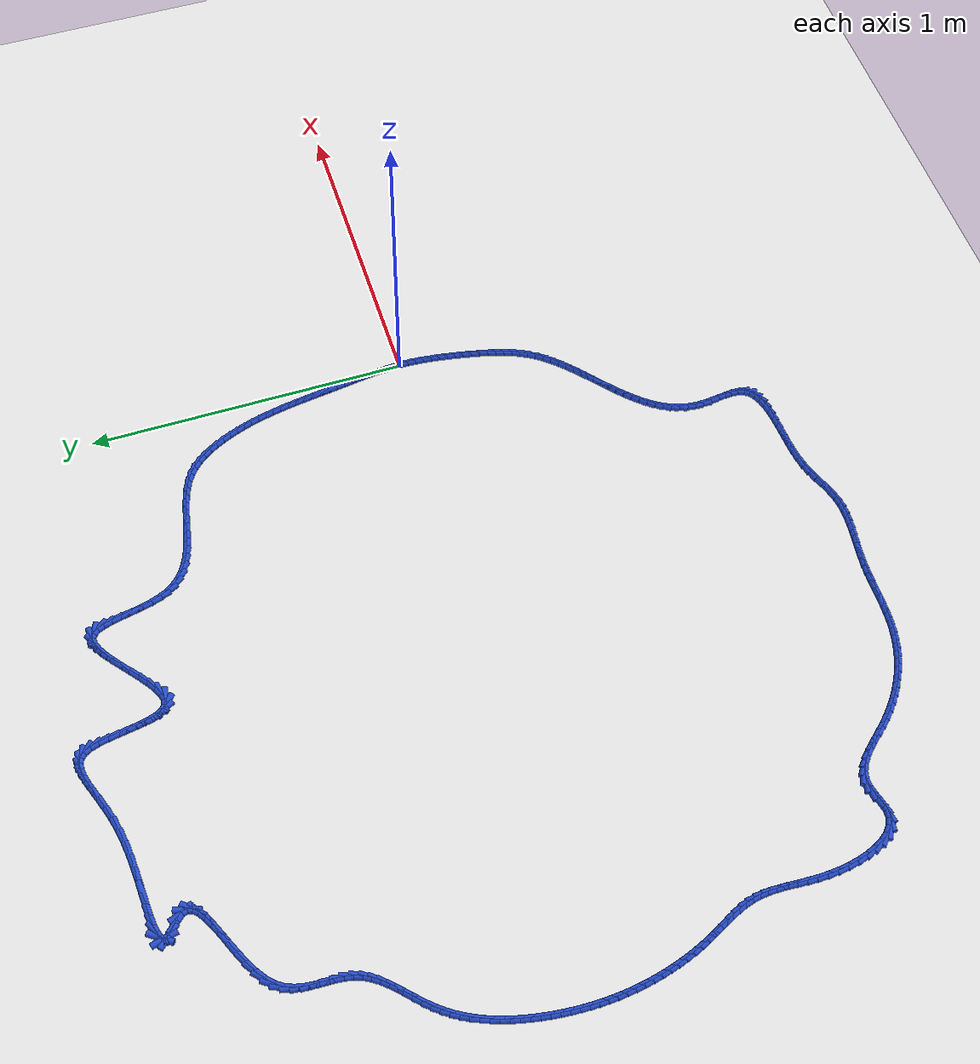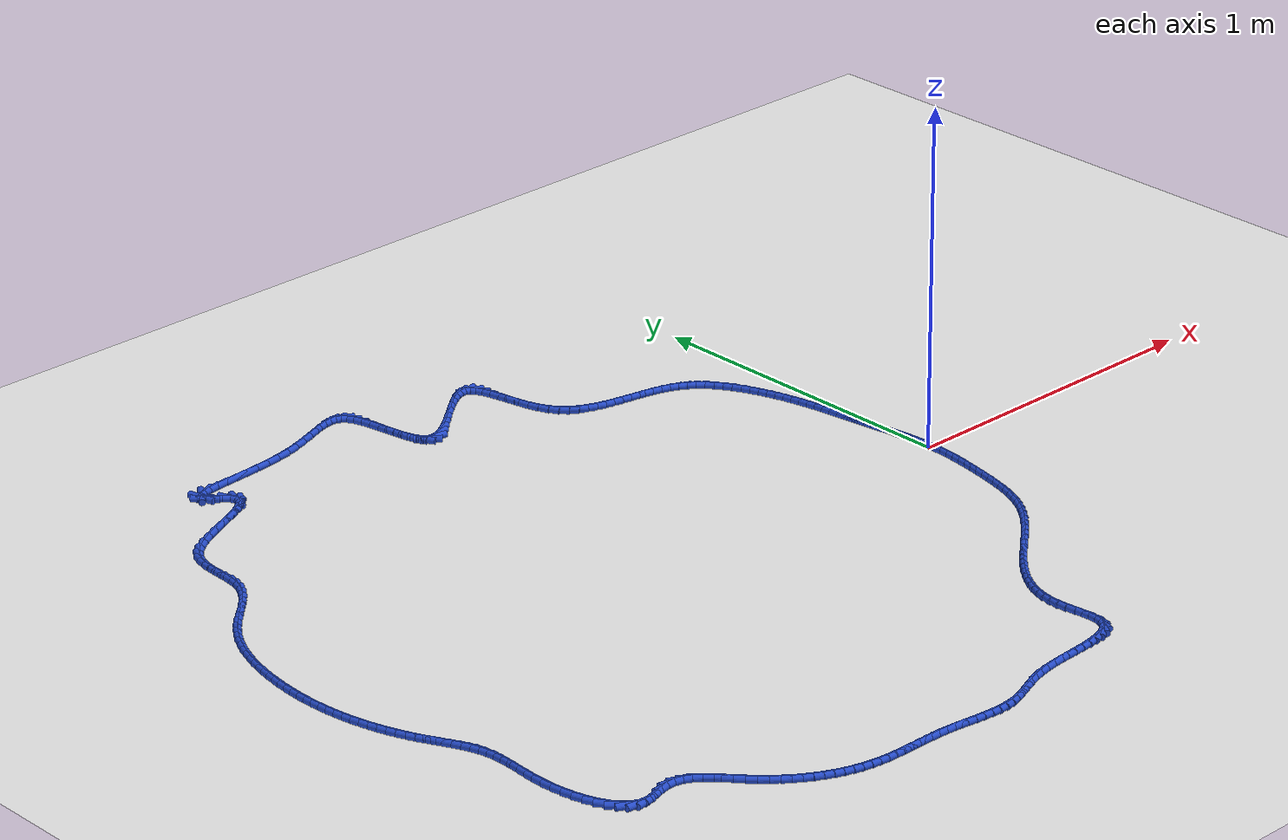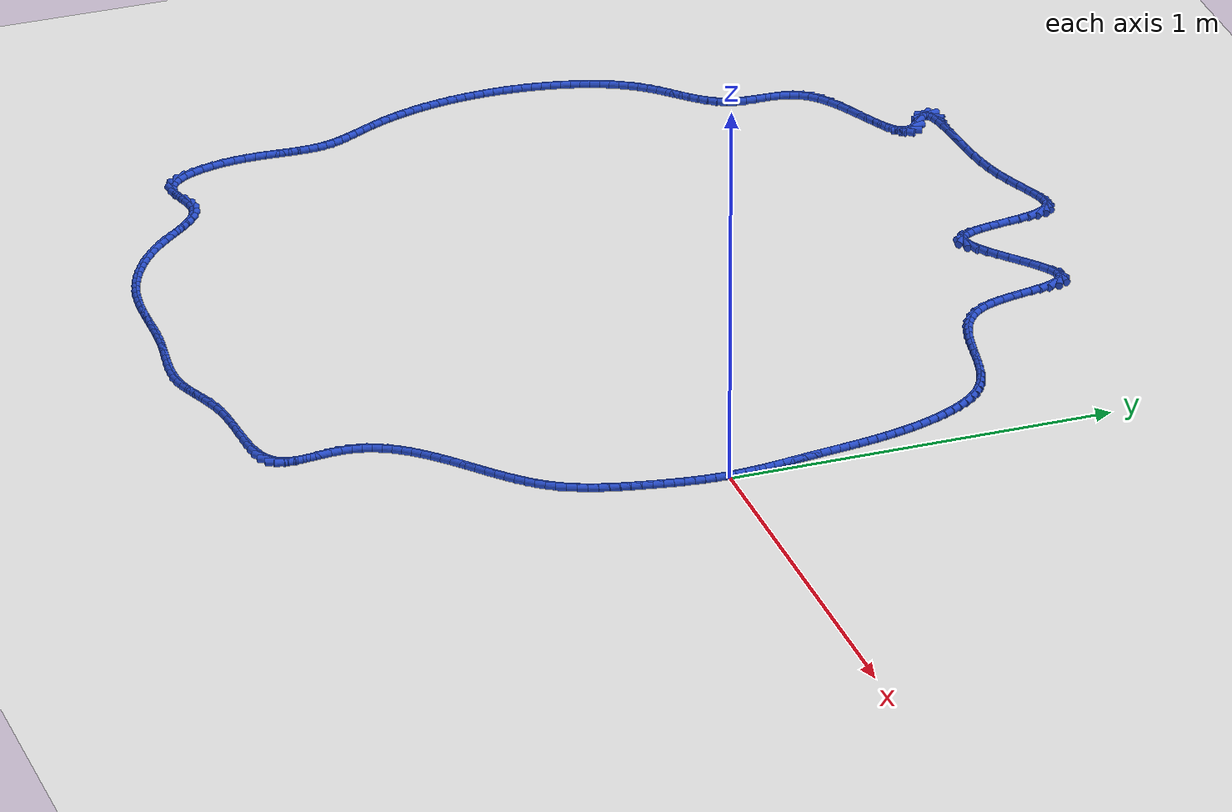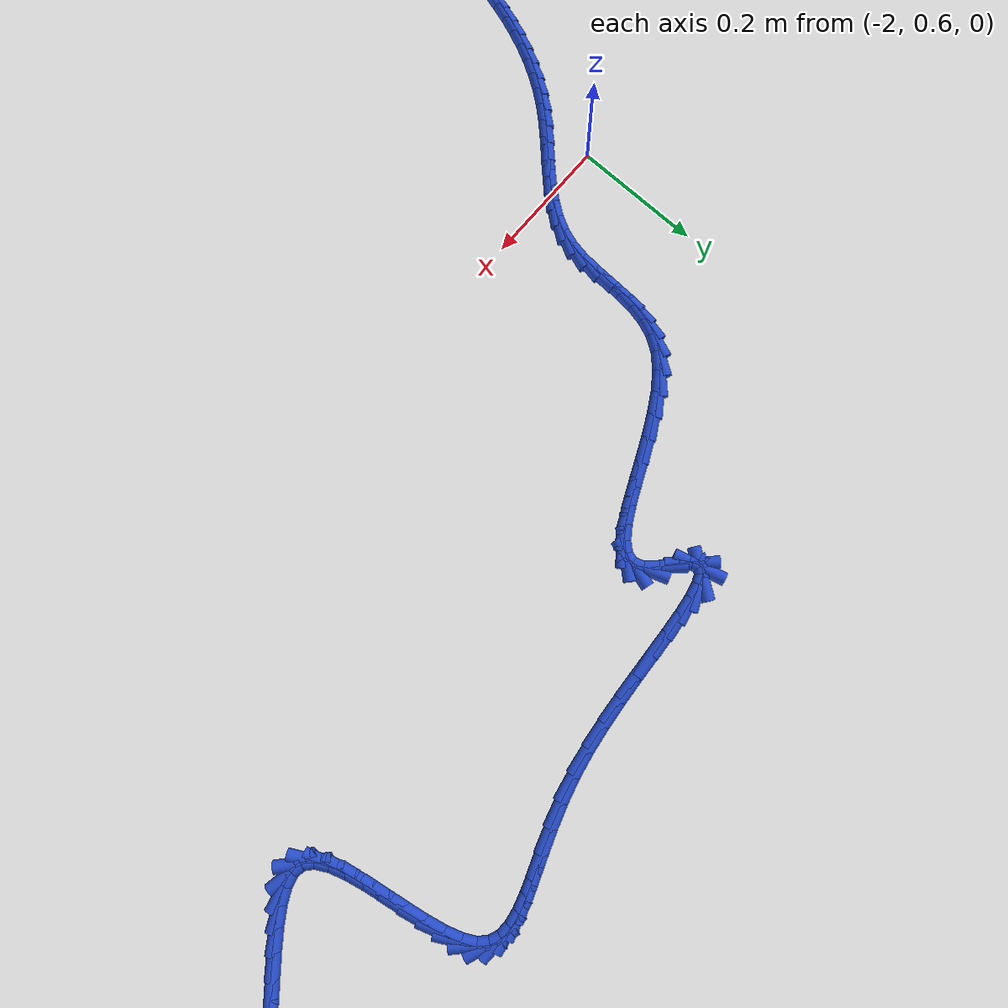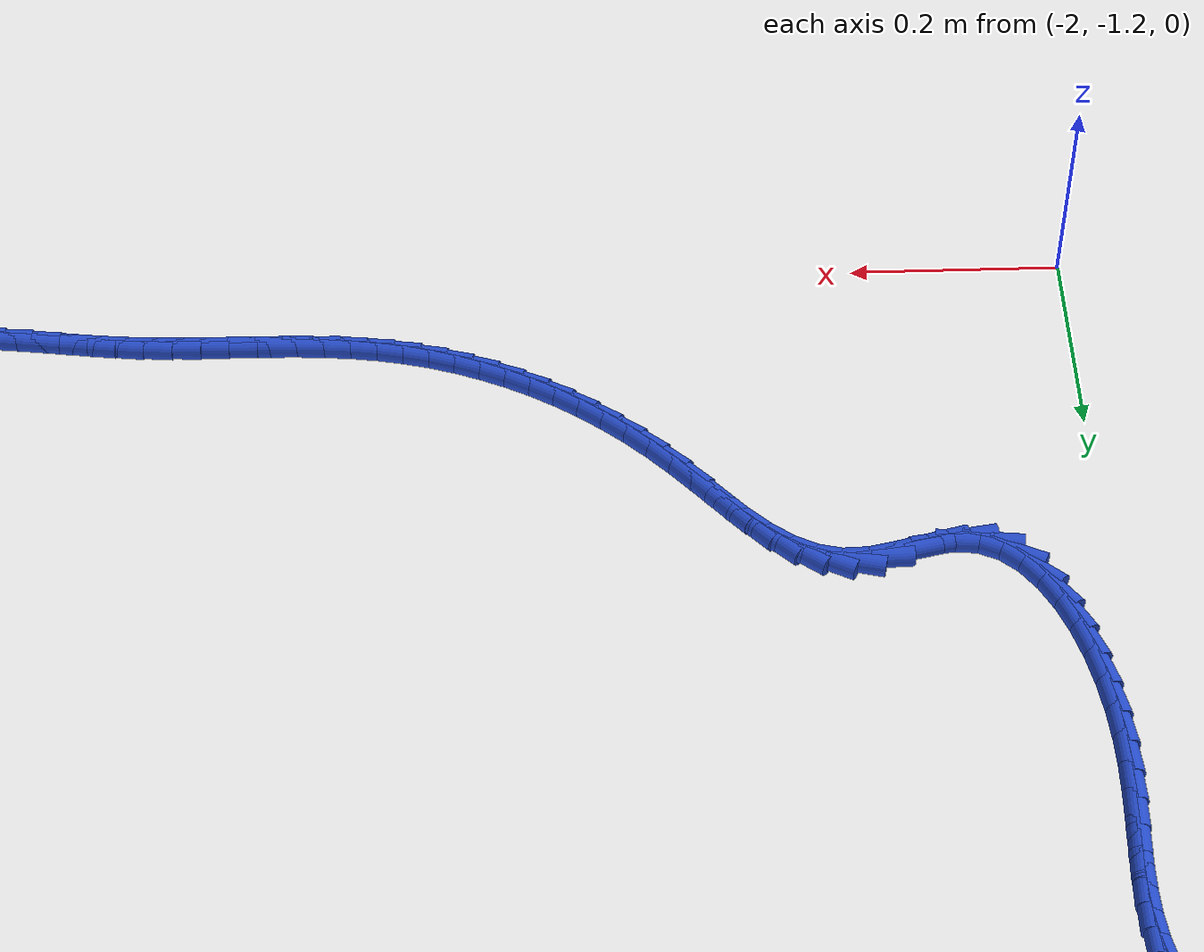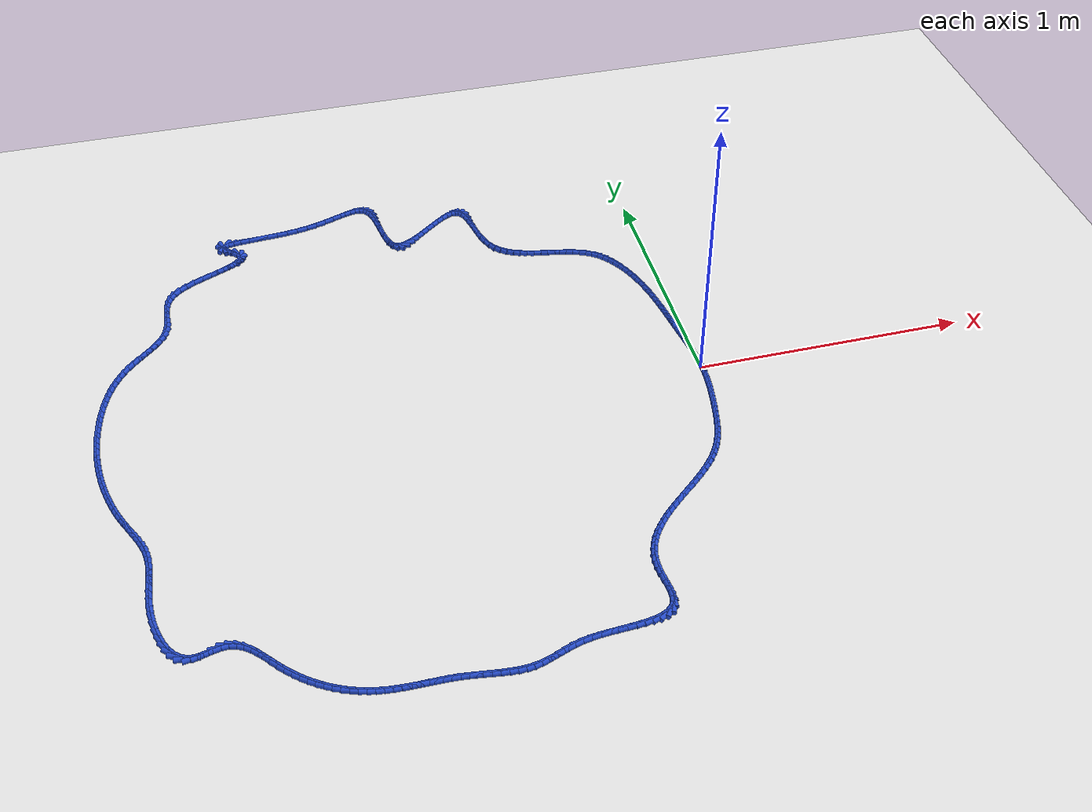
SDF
<sdf version="1.6">
 <world name="default">
  <light name="sun" type="directional">
   <pose>0 0 10 0 -0 0</pose>
   <diffuse>0.8 0.8 0.8 1</diffuse>
   <specular>0.2 0.2 0.2 1</specular>
   <attenuation>
    <range>1000</range>
    <constant>0.9</constant>
    <linear>0.01</linear>
    <quadratic>0.001</quadratic>
   </attenuation>
   <direction>-0.5 0.1 -0.9</direction>
  </light>
  <model name="ground_plane">
   <static>1</static>
   <link name="link">
    <collision name="collision">
     <geometry><plane><normal>0 0 1</normal><size>100 100</size></plane></geometry>
     <surface><friction><ode><mu>100</mu><mu2>50</mu2></ode></friction></surface>
    </collision>
    <visual name="visual">
     <cast_shadows>0</cast_shadows>
     <geometry><plane><normal>0 0 1</normal><size>100 100</size></plane></geometry>
     <material>
      <script><uri>file://media/materials/scripts/gazebo.material</uri><name>Gazebo/WhiteGlow</name></script>
     </material>
    </visual>
   </link>
  </model>
  <gravity>0 0 -9.8</gravity>
  <magnetic_field>6e-06 2.3e-05 -4.2e-05</magnetic_field>
  <atmosphere type="adiabatic"/>
  <physics name="default_physics" default="0" type="ode">
   <max_step_size>0.001</max_step_size>
   <real_time_factor>1</real_time_factor>
   <real_time_update_rate>1000</real_time_update_rate>
  </physics>
  <scene><ambient>0.4 0.4 0.4 1</ambient><background>0.7 0.7 0.7 1</background><shadows>1</shadows></scene>
  <spherical_coordinates>
   <surface_model>EARTH_WGS84</surface_model>
   <latitude_deg>0</latitude_deg>
   <longitude_deg>0</longitude_deg>
   <elevation>0</elevation>
   <heading_deg>0</heading_deg>
  </spherical_coordinates>
  <model name="line">
   <link name="link_0">
    <pose>-7.806255641895632e-18 -2.0816681711721685e-17 0.01 0 1.57 -1.5404610374931598</pose>
    <collision name="collision">
     <geometry><cylinder><radius>0.01</radius><length>0.08</length></cylinder></geometry>
    </collision>
    <visual name="visual">
     <material>
      <script><name>Gazebo/Blue</name><uri>file://media/materials/scripts/gazebo.material</uri></script>
     </material>
     <geometry><cylinder><radius>0.01</radius><length>0.08</length></cylinder></geometry>
    </visual>
   </link>
   <link name="link_1">
    <pose>-0.0007810685125720414 0.025739952653974323 0.01 0 1.57 -1.5077645329489693</pose>
    <collision name="collision">
     <geometry><cylinder><radius>0.01</radius><length>0.08</length></cylinder></geometry>
    </collision>
    <visual name="visual">
     <material>
      <script><name>Gazebo/Blue</name><uri>file://media/materials/scripts/gazebo.material</uri></script>
     </material>
     <geometry><cylinder><radius>0.01</radius><length>0.08</length></cylinder></geometry>
    </visual>
   </link>
   <link name="link_2">
    <pose>-0.0024057646785755095 0.05148162766888762 0.01 0 1.57 -1.4805571677666232</pose>
    <collision name="collision">
     <geometry><cylinder><radius>0.01</radius><length>0.08</length></cylinder></geometry>
    </collision>
    <visual name="visual">
     <material>
      <script><name>Gazebo/Blue</name><uri>file://media/materials/scripts/gazebo.material</uri></script>
     </material>
     <geometry><cylinder><radius>0.01</radius><length>0.08</length></cylinder></geometry>
    </visual>
   </link>
   <link name="link_3">
    <pose>-0.004735273473870228 0.07722635135019318 0.01 0 1.57 -1.4588159628600574</pose>
    <collision name="collision">
     <geometry><cylinder><radius>0.01</radius><length>0.08</length></cylinder></geometry>
    </collision>
    <visual name="visual">
     <material>
      <script><name>Gazebo/Blue</name><uri>file://media/materials/scripts/gazebo.material</uri></script>
     </material>
     <geometry><cylinder><radius>0.01</radius><length>0.08</length></cylinder></geometry>
    </visual>
   </link>
   <link name="link_4">
    <pose>-0.007630779874316007 0.1029754500033443 0.01 0 1.57 -1.4424926155566993</pose>
    <collision name="collision">
     <geometry><cylinder><radius>0.01</radius><length>0.08</length></cylinder></geometry>
    </collision>
    <visual name="visual">
     <material>
      <script><name>Gazebo/Blue</name><uri>file://media/materials/scripts/gazebo.material</uri></script>
     </material>
     <geometry><cylinder><radius>0.01</radius><length>0.08</length></cylinder></geometry>
    </visual>
   </link>
   <link name="link_5">
    <pose>-0.010953468855772665 0.1287302499337943 0.01 0 1.57 -1.4315328510096803</pose>
    <collision name="collision">
     <geometry><cylinder><radius>0.01</radius><length>0.08</length></cylinder></geometry>
    </collision>
    <visual name="visual">
     <material>
      <script><name>Gazebo/Blue</name><uri>file://media/materials/scripts/gazebo.material</uri></script>
     </material>
     <geometry><cylinder><radius>0.01</radius><length>0.08</length></cylinder></geometry>
    </visual>
   </link>
   <link name="link_6">
    <pose>-0.014564525394100018 0.15449207744699653 0.01 0 1.57 -1.4258904491077136</pose>
    <collision name="collision">
     <geometry><cylinder><radius>0.01</radius><length>0.08</length></cylinder></geometry>
    </collision>
    <visual name="visual">
     <material>
      <script><name>Gazebo/Blue</name><uri>file://media/materials/scripts/gazebo.material</uri></script>
     </material>
     <geometry><cylinder><radius>0.01</radius><length>0.08</length></cylinder></geometry>
    </visual>
   </link>
   <link name="link_7">
    <pose>-0.01832513446515788 0.18026225884840422 0.01 0 1.57 -1.4255362973416508</pose>
    <collision name="collision">
     <geometry><cylinder><radius>0.01</radius><length>0.08</length></cylinder></geometry>
    </collision>
    <visual name="visual">
     <material>
      <script><name>Gazebo/Blue</name><uri>file://media/materials/scripts/gazebo.material</uri></script>
     </material>
     <geometry><cylinder><radius>0.01</radius><length>0.08</length></cylinder></geometry>
    </visual>
   </link>
   <link name="link_8">
    <pose>-0.02209648104480607 0.20604212044347073 0.01 0 1.57 -1.4300593175898704</pose>
    <collision name="collision">
     <geometry><cylinder><radius>0.01</radius><length>0.08</length></cylinder></geometry>
    </collision>
    <visual name="visual">
     <material>
      <script><name>Gazebo/Blue</name><uri>file://media/materials/scripts/gazebo.material</uri></script>
     </material>
     <geometry><cylinder><radius>0.01</radius><length>0.08</length></cylinder></geometry>
    </visual>
   </link>
   <link name="link_9">
    <pose>-0.025750255485725917 0.23183220384311948 0.01 0 1.57 -1.434548371362645</pose>
    <collision name="collision">
     <geometry><cylinder><radius>0.01</radius><length>0.08</length></cylinder></geometry>
    </collision>
    <visual name="visual">
     <material>
      <script><name>Gazebo/Blue</name><uri>file://media/materials/scripts/gazebo.material</uri></script>
     </material>
     <geometry><cylinder><radius>0.01</radius><length>0.08</length></cylinder></geometry>
    </visual>
   </link>
   <link name="link_10">
    <pose>-0.029286172010129993 0.25762348797129764 0.01 0 1.57 -1.4357179457904505</pose>
    <collision name="collision">
     <geometry><cylinder><radius>0.01</radius><length>0.08</length></cylinder></geometry>
    </collision>
    <visual name="visual">
     <material>
      <script><name>Gazebo/Blue</name><uri>file://media/materials/scripts/gazebo.material</uri></script>
     </material>
     <geometry><cylinder><radius>0.01</radius><length>0.08</length></cylinder></geometry>
    </visual>
   </link>
   <link name="link_11">
    <pose>-0.0327894310130966 0.28340056639963557 0.01 0 1.57 -1.4335013348796353</pose>
    <collision name="collision">
     <geometry><cylinder><radius>0.01</radius><length>0.08</length></cylinder></geometry>
    </collision>
    <visual name="visual">
     <material>
      <script><name>Gazebo/Blue</name><uri>file://media/materials/scripts/gazebo.material</uri></script>
     </material>
     <geometry><cylinder><radius>0.01</radius><length>0.08</length></cylinder></geometry>
    </visual>
   </link>
   <link name="link_12">
    <pose>-0.03634679331964059 0.30914791614413134 0.01 0 1.57 -1.4278890659737389</pose>
    <collision name="collision">
     <geometry><cylinder><radius>0.01</radius><length>0.08</length></cylinder></geometry>
    </collision>
    <visual name="visual">
     <material>
      <script><name>Gazebo/Blue</name><uri>file://media/materials/scripts/gazebo.material</uri></script>
     </material>
     <geometry><cylinder><radius>0.01</radius><length>0.08</length></cylinder></geometry>
    </visual>
   </link>
   <link name="link_13">
    <pose>-0.04004501975477684 0.33485001422078325 0.01 0 1.57 -1.4188697028831119</pose>
    <collision name="collision">
     <geometry><cylinder><radius>0.01</radius><length>0.08</length></cylinder></geometry>
    </collision>
    <visual name="visual">
     <material>
      <script><name>Gazebo/Blue</name><uri>file://media/materials/scripts/gazebo.material</uri></script>
     </material>
     <geometry><cylinder><radius>0.01</radius><length>0.08</length></cylinder></geometry>
    </visual>
   </link>
   <link name="link_14">
    <pose>-0.043970871143520225 0.36049133764558977 0.01 0 1.57 -1.4064317796355033</pose>
    <collision name="collision">
     <geometry><cylinder><radius>0.01</radius><length>0.08</length></cylinder></geometry>
    </collision>
    <visual name="visual">
     <material>
      <script><name>Gazebo/Blue</name><uri>file://media/materials/scripts/gazebo.material</uri></script>
     </material>
     <geometry><cylinder><radius>0.01</radius><length>0.08</length></cylinder></geometry>
    </visual>
   </link>
   <link name="link_15">
    <pose>-0.048211108310885604 0.38605636343454885 0.01 0 1.57 -1.3905669526017241</pose>
    <collision name="collision">
     <geometry><cylinder><radius>0.01</radius><length>0.08</length></cylinder></geometry>
    </collision>
    <visual name="visual">
     <material>
      <script><name>Gazebo/Blue</name><uri>file://media/materials/scripts/gazebo.material</uri></script>
     </material>
     <geometry><cylinder><radius>0.01</radius><length>0.08</length></cylinder></geometry>
    </visual>
   </link>
   <link name="link_16">
    <pose>-0.052852492081887865 0.41152956860365897 0.01 0 1.57 -1.371274387821712</pose>
    <collision name="collision">
     <geometry><cylinder><radius>0.01</radius><length>0.08</length></cylinder></geometry>
    </collision>
    <visual name="visual">
     <material>
      <script><name>Gazebo/Blue</name><uri>file://media/materials/scripts/gazebo.material</uri></script>
     </material>
     <geometry><cylinder><radius>0.01</radius><length>0.08</length></cylinder></geometry>
    </visual>
   </link>
   <link name="link_17">
    <pose>-0.05798178328154187 0.4368954301689182 0.01 0 1.57 -1.3485663591753199</pose>
    <collision name="collision">
     <geometry><cylinder><radius>0.01</radius><length>0.08</length></cylinder></geometry>
    </collision>
    <visual name="visual">
     <material>
      <script><name>Gazebo/Blue</name><uri>file://media/materials/scripts/gazebo.material</uri></script>
     </material>
     <geometry><cylinder><radius>0.01</radius><length>0.08</length></cylinder></geometry>
    </visual>
   </link>
   <link name="link_18">
    <pose>-0.06368574273486247 0.46213842514632475 0.01 0 1.57 -1.3224749528913857</pose>
    <collision name="collision">
     <geometry><cylinder><radius>0.01</radius><length>0.08</length></cylinder></geometry>
    </collision>
    <visual name="visual">
     <material>
      <script><name>Gazebo/Blue</name><uri>file://media/materials/scripts/gazebo.material</uri></script>
     </material>
     <geometry><cylinder><radius>0.01</radius><length>0.08</length></cylinder></geometry>
    </visual>
   </link>
   <link name="link_19">
    <pose>-0.07005113126686455 0.48724303055187707 0.01 0 1.57 -1.2930596469748314</pose>
    <collision name="collision">
     <geometry><cylinder><radius>0.01</radius><length>0.08</length></cylinder></geometry>
    </collision>
    <visual name="visual">
     <material>
      <script><name>Gazebo/Blue</name><uri>file://media/materials/scripts/gazebo.material</uri></script>
     </material>
     <geometry><cylinder><radius>0.01</radius><length>0.08</length></cylinder></geometry>
    </visual>
   </link>
   <link name="link_20">
    <pose>-0.07716470970256303 0.5121937234015734 0.01 0 1.57 -1.2604153596693264</pose>
    <collision name="collision">
     <geometry><cylinder><radius>0.01</radius><length>0.08</length></cylinder></geometry>
    </collision>
    <visual name="visual">
     <material>
      <script><name>Gazebo/Blue</name><uri>file://media/materials/scripts/gazebo.material</uri></script>
     </material>
     <geometry><cylinder><radius>0.01</radius><length>0.08</length></cylinder></geometry>
    </visual>
   </link>
   <link name="link_21">
    <pose>-0.08511323886697272 0.5369749807114119 0.01 0 1.57 -1.2246803508958726</pose>
    <collision name="collision">
     <geometry><cylinder><radius>0.01</radius><length>0.08</length></cylinder></geometry>
    </collision>
    <visual name="visual">
     <material>
      <script><name>Gazebo/Blue</name><uri>file://media/materials/scripts/gazebo.material</uri></script>
     </material>
     <geometry><cylinder><radius>0.01</radius><length>0.08</length></cylinder></geometry>
    </visual>
   </link>
   <link name="link_22">
    <pose>-0.09398347958510848 0.5615712794973908 0.01 0 1.57 -1.1860431448297077</pose>
    <collision name="collision">
     <geometry><cylinder><radius>0.01</radius><length>0.08</length></cylinder></geometry>
    </collision>
    <visual name="visual">
     <material>
      <script><name>Gazebo/Blue</name><uri>file://media/materials/scripts/gazebo.material</uri></script>
     </material>
     <geometry><cylinder><radius>0.01</radius><length>0.08</length></cylinder></geometry>
    </visual>
   </link>
   <link name="link_23">
    <pose>-0.10386219268198521 0.5859670967755084 0.01 0 1.57 -1.144584126258298</pose>
    <collision name="collision">
     <geometry><cylinder><radius>0.01</radius><length>0.08</length></cylinder></geometry>
    </collision>
    <visual name="visual">
     <material>
      <script><name>Gazebo/Blue</name><uri>file://media/materials/scripts/gazebo.material</uri></script>
     </material>
     <geometry><cylinder><radius>0.01</radius><length>0.08</length></cylinder></geometry>
    </visual>
   </link>
   <link name="link_24">
    <pose>-0.11483722571845668 0.6101388116421479 0.01 0 1.57 -1.0965347804306003</pose>
    <collision name="collision">
     <geometry><cylinder><radius>0.01</radius><length>0.08</length></cylinder></geometry>
    </collision>
    <visual name="visual">
     <material>
      <script><name>Gazebo/Blue</name><uri>file://media/materials/scripts/gazebo.material</uri></script>
     </material>
     <geometry><cylinder><radius>0.01</radius><length>0.08</length></cylinder></geometry>
    </visual>
   </link>
   <link name="link_25">
    <pose>-0.12702169165128144 0.6338745355965881 0.01 0 1.57 -1.0370387465355602</pose>
    <collision name="collision">
     <geometry><cylinder><radius>0.01</radius><length>0.08</length></cylinder></geometry>
    </collision>
    <visual name="visual">
     <material>
      <script><name>Gazebo/Blue</name><uri>file://media/materials/scripts/gazebo.material</uri></script>
     </material>
     <geometry><cylinder><radius>0.01</radius><length>0.08</length></cylinder></geometry>
    </visual>
   </link>
   <link name="link_26">
    <pose>-0.14055412001495723 0.656772985994607 0.01 0 1.57 -0.9643003962133214</pose>
    <collision name="collision">
     <geometry><cylinder><radius>0.01</radius><length>0.08</length></cylinder></geometry>
    </collision>
    <visual name="visual">
     <material>
      <script><name>Gazebo/Blue</name><uri>file://media/materials/scripts/gazebo.material</uri></script>
     </material>
     <geometry><cylinder><radius>0.01</radius><length>0.08</length></cylinder></geometry>
    </visual>
   </link>
   <link name="link_27">
    <pose>-0.15557415731652494 0.6784245569605744 0.01 0 1.57 -0.8765091758855857</pose>
    <collision name="collision">
     <geometry><cylinder><radius>0.01</radius><length>0.08</length></cylinder></geometry>
    </collision>
    <visual name="visual">
     <material>
      <script><name>Gazebo/Blue</name><uri>file://media/materials/scripts/gazebo.material</uri></script>
     </material>
     <geometry><cylinder><radius>0.01</radius><length>0.08</length></cylinder></geometry>
    </visual>
   </link>
   <link name="link_28">
    <pose>-0.17222145006302572 0.6984196426188605 0.01 0 1.57 -0.7720484433847453</pose>
    <collision name="collision">
     <geometry><cylinder><radius>0.01</radius><length>0.08</length></cylinder></geometry>
    </collision>
    <visual name="visual">
     <material>
      <script><name>Gazebo/Blue</name><uri>file://media/materials/scripts/gazebo.material</uri></script>
     </material>
     <geometry><cylinder><radius>0.01</radius><length>0.08</length></cylinder></geometry>
    </visual>
   </link>
   <link name="link_29">
    <pose>-0.1906356447615004 0.7163486370938352 0.01 0 1.57 -0.6502314944295363</pose>
    <collision name="collision">
     <geometry><cylinder><radius>0.01</radius><length>0.08</length></cylinder></geometry>
    </collision>
    <visual name="visual">
     <material>
      <script><name>Gazebo/Blue</name><uri>file://media/materials/scripts/gazebo.material</uri></script>
     </material>
     <geometry><cylinder><radius>0.01</radius><length>0.08</length></cylinder></geometry>
    </visual>
   </link>
   <link name="link_30">
    <pose>-0.21095560658239632 0.7318033851926395 0.01 0 1.57 -0.5229237221968535</pose>
    <collision name="collision">
     <geometry><cylinder><radius>0.01</radius><length>0.08</length></cylinder></geometry>
    </collision>
    <visual name="visual">
     <material>
      <script><name>Gazebo/Blue</name><uri>file://media/materials/scripts/gazebo.material</uri></script>
     </material>
     <geometry><cylinder><radius>0.01</radius><length>0.08</length></cylinder></geometry>
    </visual>
   </link>
   <link name="link_31">
    <pose>-0.23318879074318358 0.7446197163972538 0.01 0 1.57 -0.41536183510269686</pose>
    <collision name="collision">
     <geometry><cylinder><radius>0.01</radius><length>0.08</length></cylinder></geometry>
    </collision>
    <visual name="visual">
     <material>
      <script><name>Gazebo/Blue</name><uri>file://media/materials/scripts/gazebo.material</uri></script>
     </material>
     <geometry><cylinder><radius>0.01</radius><length>0.08</length></cylinder></geometry>
    </visual>
   </link>
   <link name="link_32">
    <pose>-0.25706471528446667 0.7551494972948176 0.01 0 1.57 -0.3308768605326395</pose>
    <collision name="collision">
     <geometry><cylinder><radius>0.01</radius><length>0.08</length></cylinder></geometry>
    </collision>
    <visual name="visual">
     <material>
      <script><name>Gazebo/Blue</name><uri>file://media/materials/scripts/gazebo.material</uri></script>
     </material>
     <geometry><cylinder><radius>0.01</radius><length>0.08</length></cylinder></geometry>
    </visual>
   </link>
   <link name="link_33">
    <pose>-0.2822775476837907 0.7638102287371364 0.01 0 1.57 -0.26808662233687364</pose>
    <collision name="collision">
     <geometry><cylinder><radius>0.01</radius><length>0.08</length></cylinder></geometry>
    </collision>
    <visual name="visual">
     <material>
      <script><name>Gazebo/Blue</name><uri>file://media/materials/scripts/gazebo.material</uri></script>
     </material>
     <geometry><cylinder><radius>0.01</radius><length>0.08</length></cylinder></geometry>
    </visual>
   </link>
   <link name="link_34">
    <pose>-0.3085214554187006 0.7710194115760153 0.01 0 1.57 -0.22509022364306017</pose>
    <collision name="collision">
     <geometry><cylinder><radius>0.01</radius><length>0.08</length></cylinder></geometry>
    </collision>
    <visual name="visual">
     <material>
      <script><name>Gazebo/Blue</name><uri>file://media/materials/scripts/gazebo.material</uri></script>
     </material>
     <geometry><cylinder><radius>0.01</radius><length>0.08</length></cylinder></geometry>
    </visual>
   </link>
   <link name="link_35">
    <pose>-0.3354906059667416 0.777194546663259 0.01 0 1.57 -0.2002332795812609</pose>
    <collision name="collision">
     <geometry><cylinder><radius>0.01</radius><length>0.08</length></cylinder></geometry>
    </collision>
    <visual name="visual">
     <material>
      <script><name>Gazebo/Blue</name><uri>file://media/materials/scripts/gazebo.material</uri></script>
     </material>
     <geometry><cylinder><radius>0.01</radius><length>0.08</length></cylinder></geometry>
    </visual>
   </link>
   <link name="link_36">
    <pose>-0.3628791668054589 0.7827531348506732 0.01 0 1.57 -0.19246505629929442</pose>
    <collision name="collision">
     <geometry><cylinder><radius>0.01</radius><length>0.08</length></cylinder></geometry>
    </collision>
    <visual name="visual">
     <material>
      <script><name>Gazebo/Blue</name><uri>file://media/materials/scripts/gazebo.material</uri></script>
     </material>
     <geometry><cylinder><radius>0.01</radius><length>0.08</length></cylinder></geometry>
    </visual>
   </link>
   <link name="link_37">
    <pose>-0.39038130541239763 0.7881126769900628 0.01 0 1.57 -0.20147709216322968</pose>
    <collision name="collision">
     <geometry><cylinder><radius>0.01</radius><length>0.08</length></cylinder></geometry>
    </collision>
    <visual name="visual">
     <material>
      <script><name>Gazebo/Blue</name><uri>file://media/materials/scripts/gazebo.material</uri></script>
     </material>
     <geometry><cylinder><radius>0.01</radius><length>0.08</length></cylinder></geometry>
    </visual>
   </link>
   <link name="link_38">
    <pose>-0.4176911892651026 0.793690673933233 0.01 0 1.57 -0.22774110966531572</pose>
    <collision name="collision">
     <geometry><cylinder><radius>0.01</radius><length>0.08</length></cylinder></geometry>
    </collision>
    <visual name="visual">
     <material>
      <script><name>Gazebo/Blue</name><uri>file://media/materials/scripts/gazebo.material</uri></script>
     </material>
     <geometry><cylinder><radius>0.01</radius><length>0.08</length></cylinder></geometry>
    </visual>
   </link>
   <link name="link_39">
    <pose>-0.44450298584111936 0.7999046265319889 0.01 0 1.57 -0.27248106619999063</pose>
    <collision name="collision">
     <geometry><cylinder><radius>0.01</radius><length>0.08</length></cylinder></geometry>
    </collision>
    <visual name="visual">
     <material>
      <script><name>Gazebo/Blue</name><uri>file://media/materials/scripts/gazebo.material</uri></script>
     </material>
     <geometry><cylinder><radius>0.01</radius><length>0.08</length></cylinder></geometry>
    </visual>
   </link>
   <link name="link_40">
    <pose>-0.4705108626179928 0.8071720356381353 0.01 0 1.57 -0.3375341134608561</pose>
    <collision name="collision">
     <geometry><cylinder><radius>0.01</radius><length>0.08</length></cylinder></geometry>
    </collision>
    <visual name="visual">
     <material>
      <script><name>Gazebo/Blue</name><uri>file://media/materials/scripts/gazebo.material</uri></script>
     </material>
     <geometry><cylinder><radius>0.01</radius><length>0.08</length></cylinder></geometry>
    </visual>
   </link>
   <link name="link_41">
    <pose>-0.49540898707326814 0.8159104021034782 0.01 0 1.57 -0.4249654628243723</pose>
    <collision name="collision">
     <geometry><cylinder><radius>0.01</radius><length>0.08</length></cylinder></geometry>
    </collision>
    <visual name="visual">
     <material>
      <script><name>Gazebo/Blue</name><uri>file://media/materials/scripts/gazebo.material</uri></script>
     </material>
     <geometry><cylinder><radius>0.01</radius><length>0.08</length></cylinder></geometry>
    </visual>
   </link>
   <link name="link_42">
    <pose>-0.5188915266844903 0.8265372267798221 0.01 0 1.57 -0.536222835143369</pose>
    <collision name="collision">
     <geometry><cylinder><radius>0.01</radius><length>0.08</length></cylinder></geometry>
    </collision>
    <visual name="visual">
     <material>
      <script><name>Gazebo/Blue</name><uri>file://media/materials/scripts/gazebo.material</uri></script>
     </material>
     <geometry><cylinder><radius>0.01</radius><length>0.08</length></cylinder></geometry>
    </visual>
   </link>
   <link name="link_43">
    <pose>-0.5406526489292046 0.8394700105189723 0.01 0 1.57 -0.6706845842611207</pose>
    <collision name="collision">
     <geometry><cylinder><radius>0.01</radius><length>0.08</length></cylinder></geometry>
    </collision>
    <visual name="visual">
     <material>
      <script><name>Gazebo/Blue</name><uri>file://media/materials/scripts/gazebo.material</uri></script>
     </material>
     <geometry><cylinder><radius>0.01</radius><length>0.08</length></cylinder></geometry>
    </visual>
   </link>
   <link name="link_44">
    <pose>-0.5603865212849561 0.8551262541727339 0.01 0 1.57 -0.8239561665728614</pose>
    <collision name="collision">
     <geometry><cylinder><radius>0.01</radius><length>0.08</length></cylinder></geometry>
    </collision>
    <visual name="visual">
     <material>
      <script><name>Gazebo/Blue</name><uri>file://media/materials/scripts/gazebo.material</uri></script>
     </material>
     <geometry><cylinder><radius>0.01</radius><length>0.08</length></cylinder></geometry>
    </visual>
   </link>
   <link name="link_45">
    <pose>-0.5777873112292901 0.8739234585929123 0.01 0 1.57 -0.9872010220546819</pose>
    <collision name="collision">
     <geometry><cylinder><radius>0.01</radius><length>0.08</length></cylinder></geometry>
    </collision>
    <visual name="visual">
     <material>
      <script><name>Gazebo/Blue</name><uri>file://media/materials/scripts/gazebo.material</uri></script>
     </material>
     <geometry><cylinder><radius>0.01</radius><length>0.08</length></cylinder></geometry>
    </visual>
   </link>
   <link name="link_46">
    <pose>-0.5925491862397513 0.8962791246313124 0.01 0 1.57 -1.1441873027081468</pose>
    <collision name="collision">
     <geometry><cylinder><radius>0.01</radius><length>0.08</length></cylinder></geometry>
    </collision>
    <visual name="visual">
     <material>
      <script><name>Gazebo/Blue</name><uri>file://media/materials/scripts/gazebo.material</uri></script>
     </material>
     <geometry><cylinder><radius>0.01</radius><length>0.08</length></cylinder></geometry>
    </visual>
   </link>
   <link name="link_47">
    <pose>-0.6044505152647952 0.9224633322063294 0.01 0 1.57 -1.257912851594964</pose>
    <collision name="collision">
     <geometry><cylinder><radius>0.01</radius><length>0.08</length></cylinder></geometry>
    </collision>
    <visual name="visual">
     <material>
      <script><name>Gazebo/Blue</name><uri>file://media/materials/scripts/gazebo.material</uri></script>
     </material>
     <geometry><cylinder><radius>0.01</radius><length>0.08</length></cylinder></geometry>
    </visual>
   </link>
   <link name="link_48">
    <pose>-0.6138937971129101 0.9516534272788523 0.01 0 1.57 -1.3274149270042646</pose>
    <collision name="collision">
     <geometry><cylinder><radius>0.01</radius><length>0.08</length></cylinder></geometry>
    </collision>
    <visual name="visual">
     <material>
      <script><name>Gazebo/Blue</name><uri>file://media/materials/scripts/gazebo.material</uri></script>
     </material>
     <geometry><cylinder><radius>0.01</radius><length>0.08</length></cylinder></geometry>
    </visual>
   </link>
   <link name="link_49">
    <pose>-0.6215619844931102 0.9825357337961745 0.01 0 1.57 -1.3634028053142357</pose>
    <collision name="collision">
     <geometry><cylinder><radius>0.01</radius><length>0.08</length></cylinder></geometry>
    </collision>
    <visual name="visual">
     <material>
      <script><name>Gazebo/Blue</name><uri>file://media/materials/scripts/gazebo.material</uri></script>
     </material>
     <geometry><cylinder><radius>0.01</radius><length>0.08</length></cylinder></geometry>
    </visual>
   </link>
   <link name="link_50">
    <pose>-0.628139368449632 1.0137942325324154 0.01 0 1.57 -1.3700052944942394</pose>
    <collision name="collision">
     <geometry><cylinder><radius>0.01</radius><length>0.08</length></cylinder></geometry>
    </collision>
    <visual name="visual">
     <material>
      <script><name>Gazebo/Blue</name><uri>file://media/materials/scripts/gazebo.material</uri></script>
     </material>
     <geometry><cylinder><radius>0.01</radius><length>0.08</length></cylinder></geometry>
    </visual>
   </link>
   <link name="link_51">
    <pose>-0.6343102400267131 1.044112904261694 0.01 0 1.57 -1.3449242299833537</pose>
    <collision name="collision">
     <geometry><cylinder><radius>0.01</radius><length>0.08</length></cylinder></geometry>
    </collision>
    <visual name="visual">
     <material>
      <script><name>Gazebo/Blue</name><uri>file://media/materials/scripts/gazebo.material</uri></script>
     </material>
     <geometry><cylinder><radius>0.01</radius><length>0.08</length></cylinder></geometry>
    </visual>
   </link>
   <link name="link_52">
    <pose>-0.6407588902685908 1.0721757297581296 0.01 0 1.57 -1.2769650693977275</pose>
    <collision name="collision">
     <geometry><cylinder><radius>0.01</radius><length>0.08</length></cylinder></geometry>
    </collision>
    <visual name="visual">
     <material>
      <script><name>Gazebo/Blue</name><uri>file://media/materials/scripts/gazebo.material</uri></script>
     </material>
     <geometry><cylinder><radius>0.01</radius><length>0.08</length></cylinder></geometry>
    </visual>
   </link>
   <link name="link_53">
    <pose>-0.6481696102195021 1.096666689795842 0.01 0 1.57 -1.1379887968928584</pose>
    <collision name="collision">
     <geometry><cylinder><radius>0.01</radius><length>0.08</length></cylinder></geometry>
    </collision>
    <visual name="visual">
     <material>
      <script><name>Gazebo/Blue</name><uri>file://media/materials/scripts/gazebo.material</uri></script>
     </material>
     <geometry><cylinder><radius>0.01</radius><length>0.08</length></cylinder></geometry>
    </visual>
   </link>
   <link name="link_54">
    <pose>-0.6572266909236844 1.1162697651489504 0.01 0 1.57 -0.8663699969377535</pose>
    <collision name="collision">
     <geometry><cylinder><radius>0.01</radius><length>0.08</length></cylinder></geometry>
    </collision>
    <visual name="visual">
     <material>
      <script><name>Gazebo/Blue</name><uri>file://media/materials/scripts/gazebo.material</uri></script>
     </material>
     <geometry><cylinder><radius>0.01</radius><length>0.08</length></cylinder></geometry>
    </visual>
   </link>
   <link name="link_55">
    <pose>-0.6686144234253746 1.1296689365915744 0.01 0 1.57 -0.3878283134372157</pose>
    <collision name="collision">
     <geometry><cylinder><radius>0.01</radius><length>0.08</length></cylinder></geometry>
    </collision>
    <visual name="visual">
     <material>
      <script><name>Gazebo/Blue</name><uri>file://media/materials/scripts/gazebo.material</uri></script>
     </material>
     <geometry><cylinder><radius>0.01</radius><length>0.08</length></cylinder></geometry>
    </visual>
   </link>
   <link name="link_56">
    <pose>-0.683015350493324 1.1355519823967175 0.01 0 1.57 0.12107804830215767</pose>
    <collision name="collision">
     <geometry><cylinder><radius>0.01</radius><length>0.08</length></cylinder></geometry>
    </collision>
    <visual name="visual">
     <material>
      <script><name>Gazebo/Blue</name><uri>file://media/materials/scripts/gazebo.material</uri></script>
     </material>
     <geometry><cylinder><radius>0.01</radius><length>0.08</length></cylinder></geometry>
    </visual>
   </link>
   <link name="link_57">
    <pose>-0.7007494523329277 1.133394217436345 0.01 0 1.57 0.4111846352251826</pose>
    <collision name="collision">
     <geometry><cylinder><radius>0.01</radius><length>0.08</length></cylinder></geometry>
    </collision>
    <visual name="visual">
     <material>
      <script><name>Gazebo/Blue</name><uri>file://media/materials/scripts/gazebo.material</uri></script>
     </material>
     <geometry><cylinder><radius>0.01</radius><length>0.08</length></cylinder></geometry>
    </visual>
   </link>
   <link name="link_58">
    <pose>-0.7213317127092982 1.1244195214449506 0.01 0 1.57 0.5604641448945676</pose>
    <collision name="collision">
     <geometry><cylinder><radius>0.01</radius><length>0.08</length></cylinder></geometry>
    </collision>
    <visual name="visual">
     <material>
      <script><name>Gazebo/Blue</name><uri>file://media/materials/scripts/gazebo.material</uri></script>
     </material>
     <geometry><cylinder><radius>0.01</radius><length>0.08</length></cylinder></geometry>
    </visual>
   </link>
   <link name="link_59">
    <pose>-0.7441688003528001 1.1100870495624433 0.01 0 1.57 0.6397589733849699</pose>
    <collision name="collision">
     <geometry><cylinder><radius>0.01</radius><length>0.08</length></cylinder></geometry>
    </collision>
    <visual name="visual">
     <material>
      <script><name>Gazebo/Blue</name><uri>file://media/materials/scripts/gazebo.material</uri></script>
     </material>
     <geometry><cylinder><radius>0.01</radius><length>0.08</length></cylinder></geometry>
    </visual>
   </link>
   <link name="link_60">
    <pose>-0.768667383993798 1.0918559569287305 0.01 0 1.57 0.6798986891462775</pose>
    <collision name="collision">
     <geometry><cylinder><radius>0.01</radius><length>0.08</length></cylinder></geometry>
    </collision>
    <visual name="visual">
     <material>
      <script><name>Gazebo/Blue</name><uri>file://media/materials/scripts/gazebo.material</uri></script>
     </material>
     <geometry><cylinder><radius>0.01</radius><length>0.08</length></cylinder></geometry>
    </visual>
   </link>
   <link name="link_61">
    <pose>-0.794234132362657 1.0711853986837212 0.01 0 1.57 0.6935938818047802</pose>
    <collision name="collision">
     <geometry><cylinder><radius>0.01</radius><length>0.08</length></cylinder></geometry>
    </collision>
    <visual name="visual">
     <material>
      <script><name>Gazebo/Blue</name><uri>file://media/materials/scripts/gazebo.material</uri></script>
     </material>
     <geometry><cylinder><radius>0.01</radius><length>0.08</length></cylinder></geometry>
    </visual>
   </link>
   <link name="link_62">
    <pose>-0.8202757141897414 1.0495345299673235 0.01 0 1.57 0.6848560830334747</pose>
    <collision name="collision">
     <geometry><cylinder><radius>0.01</radius><length>0.08</length></cylinder></geometry>
    </collision>
    <visual name="visual">
     <material>
      <script><name>Gazebo/Blue</name><uri>file://media/materials/scripts/gazebo.material</uri></script>
     </material>
     <geometry><cylinder><radius>0.01</radius><length>0.08</length></cylinder></geometry>
    </visual>
   </link>
   <link name="link_63">
    <pose>-0.8461987982054161 1.0283625059194457 0.01 0 1.57 0.6517150901685885</pose>
    <collision name="collision">
     <geometry><cylinder><radius>0.01</radius><length>0.08</length></cylinder></geometry>
    </collision>
    <visual name="visual">
     <material>
      <script><name>Gazebo/Blue</name><uri>file://media/materials/scripts/gazebo.material</uri></script>
     </material>
     <geometry><cylinder><radius>0.01</radius><length>0.08</length></cylinder></geometry>
    </visual>
   </link>
   <link name="link_64">
    <pose>-0.8714100531400458 1.009128481679996 0.01 0 1.57 0.585085739823886</pose>
    <collision name="collision">
     <geometry><cylinder><radius>0.01</radius><length>0.08</length></cylinder></geometry>
    </collision>
    <visual name="visual">
     <material>
      <script><name>Gazebo/Blue</name><uri>file://media/materials/scripts/gazebo.material</uri></script>
     </material>
     <geometry><cylinder><radius>0.01</radius><length>0.08</length></cylinder></geometry>
    </visual>
   </link>
   <link name="link_65">
    <pose>-0.8953161477239951 0.9932916123888826 0.01 0 1.57 0.4628023703407595</pose>
    <collision name="collision">
     <geometry><cylinder><radius>0.01</radius><length>0.08</length></cylinder></geometry>
    </collision>
    <visual name="visual">
     <material>
      <script><name>Gazebo/Blue</name><uri>file://media/materials/scripts/gazebo.material</uri></script>
     </material>
     <geometry><cylinder><radius>0.01</radius><length>0.08</length></cylinder></geometry>
    </visual>
   </link>
   <link name="link_66">
    <pose>-0.9173237506876288 0.9823110531860142 0.01 0 1.57 0.2346390988152706</pose>
    <collision name="collision">
     <geometry><cylinder><radius>0.01</radius><length>0.08</length></cylinder></geometry>
    </collision>
    <visual name="visual">
     <material>
      <script><name>Gazebo/Blue</name><uri>file://media/materials/scripts/gazebo.material</uri></script>
     </material>
     <geometry><cylinder><radius>0.01</radius><length>0.08</length></cylinder></geometry>
    </visual>
   </link>
   <link name="link_67">
    <pose>-0.9368395307613114 0.9776459592112987 0.01 0 1.57 -0.18696353289750223</pose>
    <collision name="collision">
     <geometry><cylinder><radius>0.01</radius><length>0.08</length></cylinder></geometry>
    </collision>
    <visual name="visual">
     <material>
      <script><name>Gazebo/Blue</name><uri>file://media/materials/scripts/gazebo.material</uri></script>
     </material>
     <geometry><cylinder><radius>0.01</radius><length>0.08</length></cylinder></geometry>
    </visual>
   </link>
   <link name="link_68">
    <pose>-0.953270642931737 0.98075428016921 0.01 0 1.57 -0.7267197649322065</pose>
    <collision name="collision">
     <geometry><cylinder><radius>0.01</radius><length>0.08</length></cylinder></geometry>
    </collision>
    <visual name="visual">
     <material>
      <script><name>Gazebo/Blue</name><uri>file://media/materials/scripts/gazebo.material</uri></script>
     </material>
     <geometry><cylinder><radius>0.01</radius><length>0.08</length></cylinder></geometry>
    </visual>
   </link>
   <link name="link_69">
    <pose>-0.9663215620567284 0.9923569061376099 0.01 0 1.57 -1.0752739177945363</pose>
    <collision name="collision">
     <geometry><cylinder><radius>0.01</radius><length>0.08</length></cylinder></geometry>
    </collision>
    <visual name="visual">
     <material>
      <script><name>Gazebo/Blue</name><uri>file://media/materials/scripts/gazebo.material</uri></script>
     </material>
     <geometry><cylinder><radius>0.01</radius><length>0.08</length></cylinder></geometry>
    </visual>
   </link>
   <link name="link_70">
    <pose>-0.9764988817720812 1.0111862648533028 0.01 0 1.57 -1.2567178744612857</pose>
    <collision name="collision">
     <geometry><cylinder><radius>0.01</radius><length>0.08</length></cylinder></geometry>
    </collision>
    <visual name="visual">
     <material>
      <script><name>Gazebo/Blue</name><uri>file://media/materials/scripts/gazebo.material</uri></script>
     </material>
     <geometry><cylinder><radius>0.01</radius><length>0.08</length></cylinder></geometry>
    </visual>
   </link>
   <link name="link_71">
    <pose>-0.9844431097924018 1.035642809400504 0.01 0 1.57 -1.3513973254961056</pose>
    <collision name="collision">
     <geometry><cylinder><radius>0.01</radius><length>0.08</length></cylinder></geometry>
    </collision>
    <visual name="visual">
     <material>
      <script><name>Gazebo/Blue</name><uri>file://media/materials/scripts/gazebo.material</uri></script>
     </material>
     <geometry><cylinder><radius>0.01</radius><length>0.08</length></cylinder></geometry>
    </visual>
   </link>
   <link name="link_72">
    <pose>-0.990794753832297 1.0641269928634276 0.01 0 1.57 -1.3978670858803512</pose>
    <collision name="collision">
     <geometry><cylinder><radius>0.01</radius><length>0.08</length></cylinder></geometry>
    </collision>
    <visual name="visual">
     <material>
      <script><name>Gazebo/Blue</name><uri>file://media/materials/scripts/gazebo.material</uri></script>
     </material>
     <geometry><cylinder><radius>0.01</radius><length>0.08</length></cylinder></geometry>
    </visual>
   </link>
   <link name="link_73">
    <pose>-0.9961943216063738 1.095039268326289 0.01 0 1.57 -1.411850234811686</pose>
    <collision name="collision">
     <geometry><cylinder><radius>0.01</radius><length>0.08</length></cylinder></geometry>
    </collision>
    <visual name="visual">
     <material>
      <script><name>Gazebo/Blue</name><uri>file://media/materials/scripts/gazebo.material</uri></script>
     </material>
     <geometry><cylinder><radius>0.01</radius><length>0.08</length></cylinder></geometry>
    </visual>
   </link>
   <link name="link_74">
    <pose>-1.0012823208292378 1.126780088873302 0.01 0 1.57 -1.3976377556439792</pose>
    <collision name="collision">
     <geometry><cylinder><radius>0.01</radius><length>0.08</length></cylinder></geometry>
    </collision>
    <visual name="visual">
     <material>
      <script><name>Gazebo/Blue</name><uri>file://media/materials/scripts/gazebo.material</uri></script>
     </material>
     <geometry><cylinder><radius>0.01</radius><length>0.08</length></cylinder></geometry>
    </visual>
   </link>
   <link name="link_75">
    <pose>-1.0066992592154962 1.1577499075886817 0.01 0 1.57 -1.35109495220463</pose>
    <collision name="collision">
     <geometry><cylinder><radius>0.01</radius><length>0.08</length></cylinder></geometry>
    </collision>
    <visual name="visual">
     <material>
      <script><name>Gazebo/Blue</name><uri>file://media/materials/scripts/gazebo.material</uri></script>
     </material>
     <geometry><cylinder><radius>0.01</radius><length>0.08</length></cylinder></geometry>
    </visual>
   </link>
   <link name="link_76">
    <pose>-1.0130856444797554 1.186349177556642 0.01 0 1.57 -1.2568634506462935</pose>
    <collision name="collision">
     <geometry><cylinder><radius>0.01</radius><length>0.08</length></cylinder></geometry>
    </collision>
    <visual name="visual">
     <material>
      <script><name>Gazebo/Blue</name><uri>file://media/materials/scripts/gazebo.material</uri></script>
     </material>
     <geometry><cylinder><radius>0.01</radius><length>0.08</length></cylinder></geometry>
    </visual>
   </link>
   <link name="link_77">
    <pose>-1.021081984336622 1.2109783518613981 0.01 0 1.57 -1.0775068919032713</pose>
    <collision name="collision">
     <geometry><cylinder><radius>0.01</radius><length>0.08</length></cylinder></geometry>
    </collision>
    <visual name="visual">
     <material>
      <script><name>Gazebo/Blue</name><uri>file://media/materials/scripts/gazebo.material</uri></script>
     </material>
     <geometry><cylinder><radius>0.01</radius><length>0.08</length></cylinder></geometry>
    </visual>
   </link>
   <link name="link_78">
    <pose>-1.0313287865007021 1.230037883587165 0.01 0 1.57 -0.7561566479385837</pose>
    <collision name="collision">
     <geometry><cylinder><radius>0.01</radius><length>0.08</length></cylinder></geometry>
    </collision>
    <visual name="visual">
     <material>
      <script><name>Gazebo/Blue</name><uri>file://media/materials/scripts/gazebo.material</uri></script>
     </material>
     <geometry><cylinder><radius>0.01</radius><length>0.08</length></cylinder></geometry>
    </visual>
   </link>
   <link name="link_79">
    <pose>-1.0443586131247564 1.2423271310222634 0.01 0 1.57 -0.36205976285928765</pose>
    <collision name="collision">
     <geometry><cylinder><radius>0.01</radius><length>0.08</length></cylinder></geometry>
    </collision>
    <visual name="visual">
     <material>
      <script><name>Gazebo/Blue</name><uri>file://media/materials/scripts/gazebo.material</uri></script>
     </material>
     <geometry><cylinder><radius>0.01</radius><length>0.08</length></cylinder></geometry>
    </visual>
   </link>
   <link name="link_80">
    <pose>-1.0602443992292183 1.2483439720782028 0.01 0 1.57 -0.037126683361793325</pose>
    <collision name="collision">
     <geometry><cylinder><radius>0.01</radius><length>0.08</length></cylinder></geometry>
    </collision>
    <visual name="visual">
     <material>
      <script><name>Gazebo/Blue</name><uri>file://media/materials/scripts/gazebo.material</uri></script>
     </material>
     <geometry><cylinder><radius>0.01</radius><length>0.08</length></cylinder></geometry>
    </visual>
   </link>
   <link name="link_81">
    <pose>-1.0789367687087175 1.249038276798172 0.01 0 1.57 0.16983658937015766</pose>
    <collision name="collision">
     <geometry><cylinder><radius>0.01</radius><length>0.08</length></cylinder></geometry>
    </collision>
    <visual name="visual">
     <material>
      <script><name>Gazebo/Blue</name><uri>file://media/materials/scripts/gazebo.material</uri></script>
     </material>
     <geometry><cylinder><radius>0.01</radius><length>0.08</length></cylinder></geometry>
    </visual>
   </link>
   <link name="link_82">
    <pose>-1.1003863444192725 1.2453599190634645 0.01 0 1.57 0.2859000756634395</pose>
    <collision name="collision">
     <geometry><cylinder><radius>0.01</radius><length>0.08</length></cylinder></geometry>
    </collision>
    <visual name="visual">
     <material>
      <script><name>Gazebo/Blue</name><uri>file://media/materials/scripts/gazebo.material</uri></script>
     </material>
     <geometry><cylinder><radius>0.01</radius><length>0.08</length></cylinder></geometry>
    </visual>
   </link>
   <link name="link_83">
    <pose>-1.1245437492169035 1.2382587727553733 0.01 0 1.57 0.3429237030645823</pose>
    <collision name="collision">
     <geometry><cylinder><radius>0.01</radius><length>0.08</length></cylinder></geometry>
    </collision>
    <visual name="visual">
     <material>
      <script><name>Gazebo/Blue</name><uri>file://media/materials/scripts/gazebo.material</uri></script>
     </material>
     <geometry><cylinder><radius>0.01</radius><length>0.08</length></cylinder></geometry>
    </visual>
   </link>
   <link name="link_84">
    <pose>-1.1513596059576294 1.2286847117551924 0.01 0 1.57 0.3606390608633135</pose>
    <collision name="collision">
     <geometry><cylinder><radius>0.01</radius><length>0.08</length></cylinder></geometry>
    </collision>
    <visual name="visual">
     <material>
      <script><name>Gazebo/Blue</name><uri>file://media/materials/scripts/gazebo.material</uri></script>
     </material>
     <geometry><cylinder><radius>0.01</radius><length>0.08</length></cylinder></geometry>
    </visual>
   </link>
   <link name="link_85">
    <pose>-1.1807845374974688 1.2175876099442147 0.01 0 1.57 0.34986115694825404</pose>
    <collision name="collision">
     <geometry><cylinder><radius>0.01</radius><length>0.08</length></cylinder></geometry>
    </collision>
    <visual name="visual">
     <material>
      <script><name>Gazebo/Blue</name><uri>file://media/materials/scripts/gazebo.material</uri></script>
     </material>
     <geometry><cylinder><radius>0.01</radius><length>0.08</length></cylinder></geometry>
    </visual>
   </link>
   <link name="link_86">
    <pose>-1.2127691666924432 1.205917341203734 0.01 0 1.57 0.31639886438024023</pose>
    <collision name="collision">
     <geometry><cylinder><radius>0.01</radius><length>0.08</length></cylinder></geometry>
    </collision>
    <visual name="visual">
     <material>
      <script><name>Gazebo/Blue</name><uri>file://media/materials/scripts/gazebo.material</uri></script>
     </material>
     <geometry><cylinder><radius>0.01</radius><length>0.08</length></cylinder></geometry>
    </visual>
   </link>
   <link name="link_87">
    <pose>-1.2472641163985712 1.194623779415044 0.01 0 1.57 0.2634316069525452</pose>
    <collision name="collision">
     <geometry><cylinder><radius>0.01</radius><length>0.08</length></cylinder></geometry>
    </collision>
    <visual name="visual">
     <material>
      <script><name>Gazebo/Blue</name><uri>file://media/materials/scripts/gazebo.material</uri></script>
     </material>
     <geometry><cylinder><radius>0.01</radius><length>0.08</length></cylinder></geometry>
    </visual>
   </link>
   <link name="link_88">
    <pose>-1.2842200094718716 1.1846567984594374 0.01 0 1.57 0.1971969911282162</pose>
    <collision name="collision">
     <geometry><cylinder><radius>0.01</radius><length>0.08</length></cylinder></geometry>
    </collision>
    <visual name="visual">
     <material>
      <script><name>Gazebo/Blue</name><uri>file://media/materials/scripts/gazebo.material</uri></script>
     </material>
     <geometry><cylinder><radius>0.01</radius><length>0.08</length></cylinder></geometry>
    </visual>
   </link>
   <link name="link_89">
    <pose>-1.323477576410357 1.1768133918877728 0.01 0 1.57 0.14240186316398526</pose>
    <collision name="collision">
     <geometry><cylinder><radius>0.01</radius><length>0.08</length></cylinder></geometry>
    </collision>
    <visual name="visual">
     <material>
      <script><name>Gazebo/Blue</name><uri>file://media/materials/scripts/gazebo.material</uri></script>
     </material>
     <geometry><cylinder><radius>0.01</radius><length>0.08</length></cylinder></geometry>
    </visual>
   </link>
   <link name="link_90">
    <pose>-1.3642175712392006 1.1709724055009063 0.01 0 1.57 0.10411930980026927</pose>
    <collision name="collision">
     <geometry><cylinder><radius>0.01</radius><length>0.08</length></cylinder></geometry>
    </collision>
    <visual name="visual">
     <material>
      <script><name>Gazebo/Blue</name><uri>file://media/materials/scripts/gazebo.material</uri></script>
     </material>
     <geometry><cylinder><radius>0.01</radius><length>0.08</length></cylinder></geometry>
    </visual>
   </link>
   <link name="link_91">
    <pose>-1.4053755113679962 1.166671516200379 0.01 0 1.57 0.0794081759529195</pose>
    <collision name="collision">
     <geometry><cylinder><radius>0.01</radius><length>0.08</length></cylinder></geometry>
    </collision>
    <visual name="visual">
     <material>
      <script><name>Gazebo/Blue</name><uri>file://media/materials/scripts/gazebo.material</uri></script>
     </material>
     <geometry><cylinder><radius>0.01</radius><length>0.08</length></cylinder></geometry>
    </visual>
   </link>
   <link name="link_92">
    <pose>-1.4458865062366173 1.1634478333273761 0.01 0 1.57 0.06715206622759688</pose>
    <collision name="collision">
     <geometry><cylinder><radius>0.01</radius><length>0.08</length></cylinder></geometry>
    </collision>
    <visual name="visual">
     <material>
      <script><name>Gazebo/Blue</name><uri>file://media/materials/scripts/gazebo.material</uri></script>
     </material>
     <geometry><cylinder><radius>0.01</radius><length>0.08</length></cylinder></geometry>
    </visual>
   </link>
   <link name="link_93">
    <pose>-1.4846856652849376 1.1608384662230835 0.01 0 1.57 0.06812804816555398</pose>
    <collision name="collision">
     <geometry><cylinder><radius>0.01</radius><length>0.08</length></cylinder></geometry>
    </collision>
    <visual name="visual">
     <material>
      <script><name>Gazebo/Blue</name><uri>file://media/materials/scripts/gazebo.material</uri></script>
     </material>
     <geometry><cylinder><radius>0.01</radius><length>0.08</length></cylinder></geometry>
    </visual>
   </link>
   <link name="link_94">
    <pose>-1.520708097952829 1.1583805242286862 0.01 0 1.57 0.08584621054980361</pose>
    <collision name="collision">
     <geometry><cylinder><radius>0.01</radius><length>0.08</length></cylinder></geometry>
    </collision>
    <visual name="visual">
     <material>
      <script><name>Gazebo/Blue</name><uri>file://media/materials/scripts/gazebo.material</uri></script>
     </material>
     <geometry><cylinder><radius>0.01</radius><length>0.08</length></cylinder></geometry>
    </visual>
   </link>
   <link name="link_95">
    <pose>-1.552888913680165 1.1556111166853698 0.01 0 1.57 0.12920663128514662</pose>
    <collision name="collision">
     <geometry><cylinder><radius>0.01</radius><length>0.08</length></cylinder></geometry>
    </collision>
    <visual name="visual">
     <material>
      <script><name>Gazebo/Blue</name><uri>file://media/materials/scripts/gazebo.material</uri></script>
     </material>
     <geometry><cylinder><radius>0.01</radius><length>0.08</length></cylinder></geometry>
    </visual>
   </link>
   <link name="link_96">
    <pose>-1.5801632219068185 1.1520673529343195 0.01 0 1.57 0.22077177443539628</pose>
    <collision name="collision">
     <geometry><cylinder><radius>0.01</radius><length>0.08</length></cylinder></geometry>
    </collision>
    <visual name="visual">
     <material>
      <script><name>Gazebo/Blue</name><uri>file://media/materials/scripts/gazebo.material</uri></script>
     </material>
     <geometry><cylinder><radius>0.01</radius><length>0.08</length></cylinder></geometry>
    </visual>
   </link>
   <link name="link_97">
    <pose>-1.6014661320726626 1.1472863423167208 0.01 0 1.57 0.4264137059957595</pose>
    <collision name="collision">
     <geometry><cylinder><radius>0.01</radius><length>0.08</length></cylinder></geometry>
    </collision>
    <visual name="visual">
     <material>
      <script><name>Gazebo/Blue</name><uri>file://media/materials/scripts/gazebo.material</uri></script>
     </material>
     <geometry><cylinder><radius>0.01</radius><length>0.08</length></cylinder></geometry>
    </visual>
   </link>
   <link name="link_98">
    <pose>-1.6157327536175692 1.1408051941737591 0.01 0 1.57 0.9512342452555249</pose>
    <collision name="collision">
     <geometry><cylinder><radius>0.01</radius><length>0.08</length></cylinder></geometry>
    </collision>
    <visual name="visual">
     <material>
      <script><name>Gazebo/Blue</name><uri>file://media/materials/scripts/gazebo.material</uri></script>
     </material>
     <geometry><cylinder><radius>0.01</radius><length>0.08</length></cylinder></geometry>
    </visual>
   </link>
   <link name="link_99">
    <pose>-1.6218981959814127 1.1321610178466195 0.01 0 1.57 -1.310585917778448</pose>
    <collision name="collision">
     <geometry><cylinder><radius>0.01</radius><length>0.08</length></cylinder></geometry>
    </collision>
    <visual name="visual">
     <material>
      <script><name>Gazebo/Blue</name><uri>file://media/materials/scripts/gazebo.material</uri></script>
     </material>
     <geometry><cylinder><radius>0.01</radius><length>0.08</length></cylinder></geometry>
    </visual>
   </link>
   <link name="link_100">
    <pose>-1.6188975686040659 1.120890922676488 0.01 0 1.57 -0.8267706291129698</pose>
    <collision name="collision">
     <geometry><cylinder><radius>0.01</radius><length>0.08</length></cylinder></geometry>
    </collision>
    <visual name="visual">
     <material>
      <script><name>Gazebo/Blue</name><uri>file://media/materials/scripts/gazebo.material</uri></script>
     </material>
     <geometry><cylinder><radius>0.01</radius><length>0.08</length></cylinder></geometry>
    </visual>
   </link>
   <link name="link_101">
    <pose>-1.6056839802090814 1.1065361103567135 0.01 0 1.57 -0.6910606036491262</pose>
    <collision name="collision">
     <geometry><cylinder><radius>0.01</radius><length>0.08</length></cylinder></geometry>
    </collision>
    <visual name="visual">
     <material>
      <script><name>Gazebo/Blue</name><uri>file://media/materials/scripts/gazebo.material</uri></script>
     </material>
     <geometry><cylinder><radius>0.01</radius><length>0.08</length></cylinder></geometry>
    </visual>
   </link>
   <link name="link_102">
    <pose>-1.585119048216027 1.0895264287236603 0.01 0 1.57 -0.8102092636171482</pose>
    <collision name="collision">
     <geometry><cylinder><radius>0.01</radius><length>0.08</length></cylinder></geometry>
    </collision>
    <visual name="visual">
     <material>
      <script><name>Gazebo/Blue</name><uri>file://media/materials/scripts/gazebo.material</uri></script>
     </material>
     <geometry><cylinder><radius>0.01</radius><length>0.08</length></cylinder></geometry>
    </visual>
   </link>
   <link name="link_103">
    <pose>-1.5686833237765647 1.0722542012563676 0.01 0 1.57 -1.240061202946006</pose>
    <collision name="collision">
     <geometry><cylinder><radius>0.01</radius><length>0.08</length></cylinder></geometry>
    </collision>
    <visual name="visual">
     <material>
      <script><name>Gazebo/Blue</name><uri>file://media/materials/scripts/gazebo.material</uri></script>
     </material>
     <geometry><cylinder><radius>0.01</radius><length>0.08</length></cylinder></geometry>
    </visual>
   </link>
   <link name="link_104">
    <pose>-1.563156485364218 1.0561572284055272 0.01 0 1.57 1.2866348370111431</pose>
    <collision name="collision">
     <geometry><cylinder><radius>0.01</radius><length>0.08</length></cylinder></geometry>
    </collision>
    <visual name="visual">
     <material>
      <script><name>Gazebo/Blue</name><uri>file://media/materials/scripts/gazebo.material</uri></script>
     </material>
     <geometry><cylinder><radius>0.01</radius><length>0.08</length></cylinder></geometry>
    </visual>
   </link>
   <link name="link_105">
    <pose>-1.5675655804752293 1.0410609658085086 0.01 0 1.57 0.8417476068966783</pose>
    <collision name="collision">
     <geometry><cylinder><radius>0.01</radius><length>0.08</length></cylinder></geometry>
    </collision>
    <visual name="visual">
     <material>
      <script><name>Gazebo/Blue</name><uri>file://media/materials/scripts/gazebo.material</uri></script>
     </material>
     <geometry><cylinder><radius>0.01</radius><length>0.08</length></cylinder></geometry>
    </visual>
   </link>
   <link name="link_106">
    <pose>-1.5804097753565223 1.026681083586399 0.01 0 1.57 0.6142094414422354</pose>
    <collision name="collision">
     <geometry><cylinder><radius>0.01</radius><length>0.08</length></cylinder></geometry>
    </collision>
    <visual name="visual">
     <material>
      <script><name>Gazebo/Blue</name><uri>file://media/materials/scripts/gazebo.material</uri></script>
     </material>
     <geometry><cylinder><radius>0.01</radius><length>0.08</length></cylinder></geometry>
    </visual>
   </link>
   <link name="link_107">
    <pose>-1.6001882362550168 1.0127332518602843 0.01 0 1.57 0.5008180255063951</pose>
    <collision name="collision">
     <geometry><cylinder><radius>0.01</radius><length>0.08</length></cylinder></geometry>
    </collision>
    <visual name="visual">
     <material>
      <script><name>Gazebo/Blue</name><uri>file://media/materials/scripts/gazebo.material</uri></script>
     </material>
     <geometry><cylinder><radius>0.01</radius><length>0.08</length></cylinder></geometry>
    </visual>
   </link>
   <link name="link_108">
    <pose>-1.625400129417635 0.9989331407512511 0.01 0 1.57 0.44605110698401496</pose>
    <collision name="collision">
     <geometry><cylinder><radius>0.01</radius><length>0.08</length></cylinder></geometry>
    </collision>
    <visual name="visual">
     <material>
      <script><name>Gazebo/Blue</name><uri>file://media/materials/scripts/gazebo.material</uri></script>
     </material>
     <geometry><cylinder><radius>0.01</radius><length>0.08</length></cylinder></geometry>
    </visual>
   </link>
   <link name="link_109">
    <pose>-1.6545446210912989 0.9849964203803854 0.01 0 1.57 0.42675388072381265</pose>
    <collision name="collision">
     <geometry><cylinder><radius>0.01</radius><length>0.08</length></cylinder></geometry>
    </collision>
    <visual name="visual">
     <material>
      <script><name>Gazebo/Blue</name><uri>file://media/materials/scripts/gazebo.material</uri></script>
     </material>
     <geometry><cylinder><radius>0.01</radius><length>0.08</length></cylinder></geometry>
    </visual>
   </link>
   <link name="link_110">
    <pose>-1.6861208775229295 0.9706387608687737 0.01 0 1.57 0.43391847634310304</pose>
    <collision name="collision">
     <geometry><cylinder><radius>0.01</radius><length>0.08</length></cylinder></geometry>
    </collision>
    <visual name="visual">
     <material>
      <script><name>Gazebo/Blue</name><uri>file://media/materials/scripts/gazebo.material</uri></script>
     </material>
     <geometry><cylinder><radius>0.01</radius><length>0.08</length></cylinder></geometry>
    </visual>
   </link>
   <link name="link_111">
    <pose>-1.7186280649594485 0.9555758323375023 0.01 0 1.57 0.4657466458940102</pose>
    <collision name="collision">
     <geometry><cylinder><radius>0.01</radius><length>0.08</length></cylinder></geometry>
    </collision>
    <visual name="visual">
     <material>
      <script><name>Gazebo/Blue</name><uri>file://media/materials/scripts/gazebo.material</uri></script>
     </material>
     <geometry><cylinder><radius>0.01</radius><length>0.08</length></cylinder></geometry>
    </visual>
   </link>
   <link name="link_112">
    <pose>-1.7505653496477775 0.939523304907658 0.01 0 1.57 0.5256804532666765</pose>
    <collision name="collision">
     <geometry><cylinder><radius>0.01</radius><length>0.08</length></cylinder></geometry>
    </collision>
    <visual name="visual">
     <material>
      <script><name>Gazebo/Blue</name><uri>file://media/materials/scripts/gazebo.material</uri></script>
     </material>
     <geometry><cylinder><radius>0.01</radius><length>0.08</length></cylinder></geometry>
    </visual>
   </link>
   <link name="link_113">
    <pose>-1.7804318978348388 0.922196848700327 0.01 0 1.57 0.6228280951447669</pose>
    <collision name="collision">
     <geometry><cylinder><radius>0.01</radius><length>0.08</length></cylinder></geometry>
    </collision>
    <visual name="visual">
     <material>
      <script><name>Gazebo/Blue</name><uri>file://media/materials/scripts/gazebo.material</uri></script>
     </material>
     <geometry><cylinder><radius>0.01</radius><length>0.08</length></cylinder></geometry>
    </visual>
   </link>
   <link name="link_114">
    <pose>-1.8067268757675528 0.9033121338365956 0.01 0 1.57 0.7735924669744226</pose>
    <collision name="collision">
     <geometry><cylinder><radius>0.01</radius><length>0.08</length></cylinder></geometry>
    </collision>
    <visual name="visual">
     <material>
      <script><name>Gazebo/Blue</name><uri>file://media/materials/scripts/gazebo.material</uri></script>
     </material>
     <geometry><cylinder><radius>0.01</radius><length>0.08</length></cylinder></geometry>
    </visual>
   </link>
   <link name="link_115">
    <pose>-1.8279494496928415 0.8825848304375503 0.01 0 1.57 0.986109560297999</pose>
    <collision name="collision">
     <geometry><cylinder><radius>0.01</radius><length>0.08</length></cylinder></geometry>
    </collision>
    <visual name="visual">
     <material>
      <script><name>Gazebo/Blue</name><uri>file://media/materials/scripts/gazebo.material</uri></script>
     </material>
     <geometry><cylinder><radius>0.01</radius><length>0.08</length></cylinder></geometry>
    </visual>
   </link>
   <link name="link_116">
    <pose>-1.8430043568351748 0.8598394193925721 0.01 0 1.57 1.194696136422728</pose>
    <collision name="collision">
     <geometry><cylinder><radius>0.01</radius><length>0.08</length></cylinder></geometry>
    </collision>
    <visual name="visual">
     <material>
      <script><name>Gazebo/Blue</name><uri>file://media/materials/scripts/gazebo.material</uri></script>
     </material>
     <geometry><cylinder><radius>0.01</radius><length>0.08</length></cylinder></geometry>
    </visual>
   </link>
   <link name="link_117">
    <pose>-1.852655729742783 0.835399239361796 0.01 0 1.57 1.3580620464131121</pose>
    <collision name="collision">
     <geometry><cylinder><radius>0.01</radius><length>0.08</length></cylinder></geometry>
    </collision>
    <visual name="visual">
     <material>
      <script><name>Gazebo/Blue</name><uri>file://media/materials/scripts/gazebo.material</uri></script>
     </material>
     <geometry><cylinder><radius>0.01</radius><length>0.08</length></cylinder></geometry>
    </visual>
   </link>
   <link name="link_118">
    <pose>-1.858200243518386 0.8097305050189556 0.01 0 1.57 1.467710016279355</pose>
    <collision name="collision">
     <geometry><cylinder><radius>0.01</radius><length>0.08</length></cylinder></geometry>
    </collision>
    <visual name="visual">
     <material>
      <script><name>Gazebo/Blue</name><uri>file://media/materials/scripts/gazebo.material</uri></script>
     </material>
     <geometry><cylinder><radius>0.01</radius><length>0.08</length></cylinder></geometry>
    </visual>
   </link>
   <link name="link_119">
    <pose>-1.8609346169472485 0.7832994427573892 0.01 0 1.57 1.5251460054851158</pose>
    <collision name="collision">
     <geometry><cylinder><radius>0.01</radius><length>0.08</length></cylinder></geometry>
    </collision>
    <visual name="visual">
     <material>
      <script><name>Gazebo/Blue</name><uri>file://media/materials/scripts/gazebo.material</uri></script>
     </material>
     <geometry><cylinder><radius>0.01</radius><length>0.08</length></cylinder></geometry>
    </visual>
   </link>
   <link name="link_120">
    <pose>-1.8621555688146387 0.7565722789704353 0.01 0 1.57 1.5329995367925697</pose>
    <collision name="collision">
     <geometry><cylinder><radius>0.01</radius><length>0.08</length></cylinder></geometry>
    </collision>
    <visual name="visual">
     <material>
      <script><name>Gazebo/Blue</name><uri>file://media/materials/scripts/gazebo.material</uri></script>
     </material>
     <geometry><cylinder><radius>0.01</radius><length>0.08</length></cylinder></geometry>
    </visual>
   </link>
   <link name="link_121">
    <pose>-1.8631598179058209 0.7300152400514327 0.01 0 1.57 1.4905596284436837</pose>
    <collision name="collision">
     <geometry><cylinder><radius>0.01</radius><length>0.08</length></cylinder></geometry>
    </collision>
    <visual name="visual">
     <material>
      <script><name>Gazebo/Blue</name><uri>file://media/materials/scripts/gazebo.material</uri></script>
     </material>
     <geometry><cylinder><radius>0.01</radius><length>0.08</length></cylinder></geometry>
    </visual>
   </link>
   <link name="link_122">
    <pose>-1.865244083006061 0.7040945523937191 0.01 0 1.57 1.3929477148538822</pose>
    <collision name="collision">
     <geometry><cylinder><radius>0.01</radius><length>0.08</length></cylinder></geometry>
    </collision>
    <visual name="visual">
     <material>
      <script><name>Gazebo/Blue</name><uri>file://media/materials/scripts/gazebo.material</uri></script>
     </material>
     <geometry><cylinder><radius>0.01</radius><length>0.08</length></cylinder></geometry>
    </visual>
   </link>
   <link name="link_123">
    <pose>-1.8697050829006256 0.6792764423906333 0.01 0 1.57 1.2396146551155778</pose>
    <collision name="collision">
     <geometry><cylinder><radius>0.01</radius><length>0.08</length></cylinder></geometry>
    </collision>
    <visual name="visual">
     <material>
      <script><name>Gazebo/Blue</name><uri>file://media/materials/scripts/gazebo.material</uri></script>
     </material>
     <geometry><cylinder><radius>0.01</radius><length>0.08</length></cylinder></geometry>
    </visual>
   </link>
   <link name="link_124">
    <pose>-1.8777160002573734 0.6559784425139357 0.01 0 1.57 1.083832718466362</pose>
    <collision name="collision">
     <geometry><cylinder><radius>0.01</radius><length>0.08</length></cylinder></geometry>
    </collision>
    <visual name="visual">
     <material>
      <script><name>Gazebo/Blue</name><uri>file://media/materials/scripts/gazebo.material</uri></script>
     </material>
     <geometry><cylinder><radius>0.01</radius><length>0.08</length></cylinder></geometry>
    </visual>
   </link>
   <link name="link_125">
    <pose>-1.8892720402464327 0.6341537647993928 0.01 0 1.57 0.9605756713530434</pose>
    <collision name="collision">
     <geometry><cylinder><radius>0.01</radius><length>0.08</length></cylinder></geometry>
    </collision>
    <visual name="visual">
     <material>
      <script><name>Gazebo/Blue</name><uri>file://media/materials/scripts/gazebo.material</uri></script>
     </material>
     <geometry><cylinder><radius>0.01</radius><length>0.08</length></cylinder></geometry>
    </visual>
   </link>
   <link name="link_126">
    <pose>-1.9037153769650421 0.6134982176625287 0.01 0 1.57 0.8709692458482133</pose>
    <collision name="collision">
     <geometry><cylinder><radius>0.01</radius><length>0.08</length></cylinder></geometry>
    </collision>
    <visual name="visual">
     <material>
      <script><name>Gazebo/Blue</name><uri>file://media/materials/scripts/gazebo.material</uri></script>
     </material>
     <geometry><cylinder><radius>0.01</radius><length>0.08</length></cylinder></geometry>
    </visual>
   </link>
   <link name="link_127">
    <pose>-1.9203812338829225 0.5937048698074501 0.01 0 1.57 0.8124719996282539</pose>
    <collision name="collision">
     <geometry><cylinder><radius>0.01</radius><length>0.08</length></cylinder></geometry>
    </collision>
    <visual name="visual">
     <material>
      <script><name>Gazebo/Blue</name><uri>file://media/materials/scripts/gazebo.material</uri></script>
     </material>
     <geometry><cylinder><radius>0.01</radius><length>0.08</length></cylinder></geometry>
    </visual>
   </link>
   <link name="link_128">
    <pose>-1.9386048344697928 0.5744667899382634 0.01 0 1.57 0.7820699987151097</pose>
    <collision name="collision">
     <geometry><cylinder><radius>0.01</radius><length>0.08</length></cylinder></geometry>
    </collision>
    <visual name="visual">
     <material>
      <script><name>Gazebo/Blue</name><uri>file://media/materials/scripts/gazebo.material</uri></script>
     </material>
     <geometry><cylinder><radius>0.01</radius><length>0.08</length></cylinder></geometry>
    </visual>
   </link>
   <link name="link_129">
    <pose>-1.9577214021953737 0.5554770467590753 0.01 0 1.57 0.777677643581501</pose>
    <collision name="collision">
     <geometry><cylinder><radius>0.01</radius><length>0.08</length></cylinder></geometry>
    </collision>
    <visual name="visual">
     <material>
      <script><name>Gazebo/Blue</name><uri>file://media/materials/scripts/gazebo.material</uri></script>
     </material>
     <geometry><cylinder><radius>0.01</radius><length>0.08</length></cylinder></geometry>
    </visual>
   </link>
   <link name="link_130">
    <pose>-1.9770661605293862 0.5364287089739924 0.01 0 1.57 0.79859323279427</pose>
    <collision name="collision">
     <geometry><cylinder><radius>0.01</radius><length>0.08</length></cylinder></geometry>
    </collision>
    <visual name="visual">
     <material>
      <script><name>Gazebo/Blue</name><uri>file://media/materials/scripts/gazebo.material</uri></script>
     </material>
     <geometry><cylinder><radius>0.01</radius><length>0.08</length></cylinder></geometry>
    </visual>
   </link>
   <link name="link_131">
    <pose>-1.9959743329415505 0.5170148452871215 0.01 0 1.57 0.8454749350889651</pose>
    <collision name="collision">
     <geometry><cylinder><radius>0.01</radius><length>0.08</length></cylinder></geometry>
    </collision>
    <visual name="visual">
     <material>
      <script><name>Gazebo/Blue</name><uri>file://media/materials/scripts/gazebo.material</uri></script>
     </material>
     <geometry><cylinder><radius>0.01</radius><length>0.08</length></cylinder></geometry>
    </visual>
   </link>
   <link name="link_132">
    <pose>-2.0137813187298286 0.4969286146280831 0.01 0 1.57 0.9127988594006694</pose>
    <collision name="collision">
     <geometry><cylinder><radius>0.01</radius><length>0.08</length></cylinder></geometry>
    </collision>
    <visual name="visual">
     <material>
      <script><name>Gazebo/Blue</name><uri>file://media/materials/scripts/gazebo.material</uri></script>
     </material>
     <geometry><cylinder><radius>0.01</radius><length>0.08</length></cylinder></geometry>
    </visual>
   </link>
   <link name="link_133">
    <pose>-2.029994578981996 0.47595146870179905 0.01 0 1.57 0.9807215647862473</pose>
    <collision name="collision">
     <geometry><cylinder><radius>0.01</radius><length>0.08</length></cylinder></geometry>
    </collision>
    <visual name="visual">
     <material>
      <script><name>Gazebo/Blue</name><uri>file://media/materials/scripts/gazebo.material</uri></script>
     </material>
     <geometry><cylinder><radius>0.01</radius><length>0.08</length></cylinder></geometry>
    </visual>
   </link>
   <link name="link_134">
    <pose>-2.044615466202644 0.45411829749216537 0.01 0 1.57 1.0450587749981006</pose>
    <collision name="collision">
     <geometry><cylinder><radius>0.01</radius><length>0.08</length></cylinder></geometry>
    </collision>
    <visual name="visual">
     <material>
      <script><name>Gazebo/Blue</name><uri>file://media/materials/scripts/gazebo.material</uri></script>
     </material>
     <geometry><cylinder><radius>0.01</radius><length>0.08</length></cylinder></geometry>
    </visual>
   </link>
   <link name="link_135">
    <pose>-2.0577333994141616 0.431509181941955 0.01 0 1.57 1.1053684119010048</pose>
    <collision name="collision">
     <geometry><cylinder><radius>0.01</radius><length>0.08</length></cylinder></geometry>
    </collision>
    <visual name="visual">
     <material>
      <script><name>Gazebo/Blue</name><uri>file://media/materials/scripts/gazebo.material</uri></script>
     </material>
     <geometry><cylinder><radius>0.01</radius><length>0.08</length></cylinder></geometry>
    </visual>
   </link>
   <link name="link_136">
    <pose>-2.0694377976389373 0.40820420299393967 0.01 0 1.57 1.1613740869111846</pose>
    <collision name="collision">
     <geometry><cylinder><radius>0.01</radius><length>0.08</length></cylinder></geometry>
    </collision>
    <visual name="visual">
     <material>
      <script><name>Gazebo/Blue</name><uri>file://media/materials/scripts/gazebo.material</uri></script>
     </material>
     <geometry><cylinder><radius>0.01</radius><length>0.08</length></cylinder></geometry>
    </visual>
   </link>
   <link name="link_137">
    <pose>-2.0798180798993617 0.3842834415908922 0.01 0 1.57 1.2129432572887806</pose>
    <collision name="collision">
     <geometry><cylinder><radius>0.01</radius><length>0.08</length></cylinder></geometry>
    </collision>
    <visual name="visual">
     <material>
      <script><name>Gazebo/Blue</name><uri>file://media/materials/scripts/gazebo.material</uri></script>
     </material>
     <geometry><cylinder><radius>0.01</radius><length>0.08</length></cylinder></geometry>
    </visual>
   </link>
   <link name="link_138">
    <pose>-2.0889636652178236 0.35982697867558444 0.01 0 1.57 1.2600581287095534</pose>
    <collision name="collision">
     <geometry><cylinder><radius>0.01</radius><length>0.08</length></cylinder></geometry>
    </collision>
    <visual name="visual">
     <material>
      <script><name>Gazebo/Blue</name><uri>file://media/materials/scripts/gazebo.material</uri></script>
     </material>
     <geometry><cylinder><radius>0.01</radius><length>0.08</length></cylinder></geometry>
    </visual>
   </link>
   <link name="link_139">
    <pose>-2.096963972616712 0.33491489519078893 0.01 0 1.57 1.3027848509942759</pose>
    <collision name="collision">
     <geometry><cylinder><radius>0.01</radius><length>0.08</length></cylinder></geometry>
    </collision>
    <visual name="visual">
     <material>
      <script><name>Gazebo/Blue</name><uri>file://media/materials/scripts/gazebo.material</uri></script>
     </material>
     <geometry><cylinder><radius>0.01</radius><length>0.08</length></cylinder></geometry>
    </visual>
   </link>
   <link name="link_140">
    <pose>-2.1039084211184167 0.3096272720792782 0.01 0 1.57 1.3412447667785694</pose>
    <collision name="collision">
     <geometry><cylinder><radius>0.01</radius><length>0.08</length></cylinder></geometry>
    </collision>
    <visual name="visual">
     <material>
      <script><name>Gazebo/Blue</name><uri>file://media/materials/scripts/gazebo.material</uri></script>
     </material>
     <geometry><cylinder><radius>0.01</radius><length>0.08</length></cylinder></geometry>
    </visual>
   </link>
   <link name="link_141">
    <pose>-2.1098864297453273 0.2840441902838237 0.01 0 1.57 1.3755896923211488</pose>
    <collision name="collision">
     <geometry><cylinder><radius>0.01</radius><length>0.08</length></cylinder></geometry>
    </collision>
    <visual name="visual">
     <material>
      <script><name>Gazebo/Blue</name><uri>file://media/materials/scripts/gazebo.material</uri></script>
     </material>
     <geometry><cylinder><radius>0.01</radius><length>0.08</length></cylinder></geometry>
    </visual>
   </link>
   <link name="link_142">
    <pose>-2.1149874175198327 0.2582457307471982 0.01 0 1.57 1.4060899568483347</pose>
    <collision name="collision">
     <geometry><cylinder><radius>0.01</radius><length>0.08</length></cylinder></geometry>
    </collision>
    <visual name="visual">
     <material>
      <script><name>Gazebo/Blue</name><uri>file://media/materials/scripts/gazebo.material</uri></script>
     </material>
     <geometry><cylinder><radius>0.01</radius><length>0.08</length></cylinder></geometry>
    </visual>
   </link>
   <link name="link_143">
    <pose>-2.1192981994848217 0.2323103036630744 0.01 0 1.57 1.4348867730377042</pose>
    <collision name="collision">
     <geometry><cylinder><radius>0.01</radius><length>0.08</length></cylinder></geometry>
    </collision>
    <visual name="visual">
     <material>
      <script><name>Gazebo/Blue</name><uri>file://media/materials/scripts/gazebo.material</uri></script>
     </material>
     <geometry><cylinder><radius>0.01</radius><length>0.08</length></cylinder></geometry>
    </visual>
   </link>
   <link name="link_144">
    <pose>-2.122857191053365 0.20628526535625236 0.01 0 1.57 1.4637958824350858</pose>
    <collision name="collision">
     <geometry><cylinder><radius>0.01</radius><length>0.08</length></cylinder></geometry>
    </collision>
    <visual name="visual">
     <material>
      <script><name>Gazebo/Blue</name><uri>file://media/materials/scripts/gazebo.material</uri></script>
     </material>
     <geometry><cylinder><radius>0.01</radius><length>0.08</length></cylinder></geometry>
    </visual>
   </link>
   <link name="link_145">
    <pose>-2.125660043758851 0.18019053425754214 0.01 0 1.57 1.4928950526916425</pose>
    <collision name="collision">
     <geometry><cylinder><radius>0.01</radius><length>0.08</length></cylinder></geometry>
    </collision>
    <visual name="visual">
     <material>
      <script><name>Gazebo/Blue</name><uri>file://media/materials/scripts/gazebo.material</uri></script>
     </material>
     <geometry><cylinder><radius>0.01</radius><length>0.08</length></cylinder></geometry>
    </visual>
   </link>
   <link name="link_146">
    <pose>-2.1277009377232265 0.15404508471991477 0.01 0 1.57 1.5222000940625562</pose>
    <collision name="collision">
     <geometry><cylinder><radius>0.01</radius><length>0.08</length></cylinder></geometry>
    </collision>
    <visual name="visual">
     <material>
      <script><name>Gazebo/Blue</name><uri>file://media/materials/scripts/gazebo.material</uri></script>
     </material>
     <geometry><cylinder><radius>0.01</radius><length>0.08</length></cylinder></geometry>
    </visual>
   </link>
   <link name="link_147">
    <pose>-2.1289740530684416 0.12786789109634136 0.01 0 1.57 1.5517258040849564</pose>
    <collision name="collision">
     <geometry><cylinder><radius>0.01</radius><length>0.08</length></cylinder></geometry>
    </collision>
    <visual name="visual">
     <material>
      <script><name>Gazebo/Blue</name><uri>file://media/materials/scripts/gazebo.material</uri></script>
     </material>
     <geometry><cylinder><radius>0.01</radius><length>0.08</length></cylinder></geometry>
    </visual>
   </link>
   <link name="link_148">
    <pose>-2.129473569916441 0.10167792773979288 0.01 0 1.57 -1.5601068429430243</pose>
    <collision name="collision">
     <geometry><cylinder><radius>0.01</radius><length>0.08</length></cylinder></geometry>
    </collision>
    <visual name="visual">
     <material>
      <script><name>Gazebo/Blue</name><uri>file://media/materials/scripts/gazebo.material</uri></script>
     </material>
     <geometry><cylinder><radius>0.01</radius><length>0.08</length></cylinder></geometry>
    </visual>
   </link>
   <link name="link_149">
    <pose>-2.1291936683891755 0.07549416900324046 0.01 0 1.57 -1.5301002451505998</pose>
    <collision name="collision">
     <geometry><cylinder><radius>0.01</radius><length>0.08</length></cylinder></geometry>
    </collision>
    <visual name="visual">
     <material>
      <script><name>Gazebo/Blue</name><uri>file://media/materials/scripts/gazebo.material</uri></script>
     </material>
     <geometry><cylinder><radius>0.01</radius><length>0.08</length></cylinder></geometry>
    </visual>
   </link>
   <link name="link_150">
    <pose>-2.12812852860859 0.049335589239655156 0.01 0 1.57 -1.4998362639079448</pose>
    <collision name="collision">
     <geometry><cylinder><radius>0.01</radius><length>0.08</length></cylinder></geometry>
    </collision>
    <visual name="visual">
     <material>
      <script><name>Gazebo/Blue</name><uri>file://media/materials/scripts/gazebo.material</uri></script>
     </material>
     <geometry><cylinder><radius>0.01</radius><length>0.08</length></cylinder></geometry>
    </visual>
   </link>
   <link name="link_151">
    <pose>-2.1262723306966347 0.02322116280200804 0.01 0 1.57 -1.4693057831443235</pose>
    <collision name="collision">
     <geometry><cylinder><radius>0.01</radius><length>0.08</length></cylinder></geometry>
    </collision>
    <visual name="visual">
     <material>
      <script><name>Gazebo/Blue</name><uri>file://media/materials/scripts/gazebo.material</uri></script>
     </material>
     <geometry><cylinder><radius>0.01</radius><length>0.08</length></cylinder></geometry>
    </visual>
   </link>
   <link name="link_152">
    <pose>-2.1236192547752557 -0.00283013595672902 0.01 0 1.57 -1.4385015392262326</pose>
    <collision name="collision">
     <geometry><cylinder><radius>0.01</radius><length>0.08</length></cylinder></geometry>
    </collision>
    <visual name="visual">
     <material>
      <script><name>Gazebo/Blue</name><uri>file://media/materials/scripts/gazebo.material</uri></script>
     </material>
     <geometry><cylinder><radius>0.01</radius><length>0.08</length></cylinder></geometry>
    </visual>
   </link>
   <link name="link_153">
    <pose>-2.1201634809664016 -0.028799332683586636 0.01 0 1.57 -1.4074182975557803</pose>
    <collision name="collision">
     <geometry><cylinder><radius>0.01</radius><length>0.08</length></cylinder></geometry>
    </collision>
    <visual name="visual">
     <material>
      <script><name>Gazebo/Blue</name><uri>file://media/materials/scripts/gazebo.material</uri></script>
     </material>
     <geometry><cylinder><radius>0.01</radius><length>0.08</length></cylinder></geometry>
    </visual>
   </link>
   <link name="link_154">
    <pose>-2.11589918939202 -0.05466745302559287 0.01 0 1.57 -1.376053026657823</pose>
    <collision name="collision">
     <geometry><cylinder><radius>0.01</radius><length>0.08</length></cylinder></geometry>
    </collision>
    <visual name="visual">
     <material>
      <script><name>Gazebo/Blue</name><uri>file://media/materials/scripts/gazebo.material</uri></script>
     </material>
     <geometry><cylinder><radius>0.01</radius><length>0.08</length></cylinder></geometry>
    </visual>
   </link>
   <link name="link_155">
    <pose>-2.110820560174058 -0.08041552262977666 0.01 0 1.57 -1.3444050664085256</pose>
    <collision name="collision">
     <geometry><cylinder><radius>0.01</radius><length>0.08</length></cylinder></geometry>
    </collision>
    <visual name="visual">
     <material>
      <script><name>Gazebo/Blue</name><uri>file://media/materials/scripts/gazebo.material</uri></script>
     </material>
     <geometry><cylinder><radius>0.01</radius><length>0.08</length></cylinder></geometry>
    </visual>
   </link>
   <link name="link_156">
    <pose>-2.1049217734344654 -0.106024567143167 0.01 0 1.57 -1.3124762865581647</pose>
    <collision name="collision">
     <geometry><cylinder><radius>0.01</radius><length>0.08</length></cylinder></geometry>
    </collision>
    <visual name="visual">
     <material>
      <script><name>Gazebo/Blue</name><uri>file://media/materials/scripts/gazebo.material</uri></script>
     </material>
     <geometry><cylinder><radius>0.01</radius><length>0.08</length></cylinder></geometry>
    </visual>
   </link>
   <link name="link_157">
    <pose>-2.0981970092951876 -0.13147561221279275 0.01 0 1.57 -1.2802712312546942</pose>
    <collision name="collision">
     <geometry><cylinder><radius>0.01</radius><length>0.08</length></cylinder></geometry>
    </collision>
    <visual name="visual">
     <material>
      <script><name>Gazebo/Blue</name><uri>file://media/materials/scripts/gazebo.material</uri></script>
     </material>
     <geometry><cylinder><radius>0.01</radius><length>0.08</length></cylinder></geometry>
    </visual>
   </link>
   <link name="link_158">
    <pose>-2.090640447878174 -0.15674968348568297 0.01 0 1.57 -1.247797244909269</pose>
    <collision name="collision">
     <geometry><cylinder><radius>0.01</radius><length>0.08</length></cylinder></geometry>
    </collision>
    <visual name="visual">
     <material>
      <script><name>Gazebo/Blue</name><uri>file://media/materials/scripts/gazebo.material</uri></script>
     </material>
     <geometry><cylinder><radius>0.01</radius><length>0.08</length></cylinder></geometry>
    </visual>
   </link>
   <link name="link_159">
    <pose>-2.082246269305372 -0.1818278066088665 0.01 0 1.57 -1.2150645745072455</pose>
    <collision name="collision">
     <geometry><cylinder><radius>0.01</radius><length>0.08</length></cylinder></geometry>
    </collision>
    <visual name="visual">
     <material>
      <script><name>Gazebo/Blue</name><uri>file://media/materials/scripts/gazebo.material</uri></script>
     </material>
     <geometry><cylinder><radius>0.01</radius><length>0.08</length></cylinder></geometry>
    </visual>
   </link>
   <link name="link_160">
    <pose>-2.0730086536987287 -0.20669100722937223 0.01 0 1.57 -1.1820864433810565</pose>
    <collision name="collision">
     <geometry><cylinder><radius>0.01</radius><length>0.08</length></cylinder></geometry>
    </collision>
    <visual name="visual">
     <material>
      <script><name>Gazebo/Blue</name><uri>file://media/materials/scripts/gazebo.material</uri></script>
     </material>
     <geometry><cylinder><radius>0.01</radius><length>0.08</length></cylinder></geometry>
    </visual>
   </link>
   <link name="link_161">
    <pose>-2.0629217811801928 -0.23132031099422917 0.01 0 1.57 -1.148880577814231</pose>
    <collision name="collision">
     <geometry><cylinder><radius>0.01</radius><length>0.08</length></cylinder></geometry>
    </collision>
    <visual name="visual">
     <material>
      <script><name>Gazebo/Blue</name><uri>file://media/materials/scripts/gazebo.material</uri></script>
     </material>
     <geometry><cylinder><radius>0.01</radius><length>0.08</length></cylinder></geometry>
    </visual>
   </link>
   <link name="link_162">
    <pose>-2.0519798731160246 -0.2556967486403476 0.01 0 1.57 -1.119617927656252</pose>
    <collision name="collision">
     <geometry><cylinder><radius>0.01</radius><length>0.08</length></cylinder></geometry>
    </collision>
    <visual name="visual">
     <material>
      <script><name>Gazebo/Blue</name><uri>file://media/materials/scripts/gazebo.material</uri></script>
     </material>
     <geometry><cylinder><radius>0.01</radius><length>0.08</length></cylinder></geometry>
    </visual>
   </link>
   <link name="link_163">
    <pose>-2.040293984282616 -0.2798157690905836 0.01 0 1.57 -1.1073234621754284</pose>
    <collision name="collision">
     <geometry><cylinder><radius>0.01</radius><length>0.08</length></cylinder></geometry>
    </collision>
    <visual name="visual">
     <material>
      <script><name>Gazebo/Blue</name><uri>file://media/materials/scripts/gazebo.material</uri></script>
     </material>
     <geometry><cylinder><radius>0.01</radius><length>0.08</length></cylinder></geometry>
    </visual>
   </link>
   <link name="link_164">
    <pose>-2.0283476926992847 -0.3037187936431595 0.01 0 1.57 -1.114582584850872</pose>
    <collision name="collision">
     <geometry><cylinder><radius>0.01</radius><length>0.08</length></cylinder></geometry>
    </collision>
    <visual name="visual">
     <material>
      <script><name>Gazebo/Blue</name><uri>file://media/materials/scripts/gazebo.material</uri></script>
     </material>
     <geometry><cylinder><radius>0.01</radius><length>0.08</length></cylinder></geometry>
    </visual>
   </link>
   <link name="link_165">
    <pose>-2.0166986612210454 -0.3274563862630715 0.01 0 1.57 -1.1421881804024092</pose>
    <collision name="collision">
     <geometry><cylinder><radius>0.01</radius><length>0.08</length></cylinder></geometry>
    </collision>
    <visual name="visual">
     <material>
      <script><name>Gazebo/Blue</name><uri>file://media/materials/scripts/gazebo.material</uri></script>
     </material>
     <geometry><cylinder><radius>0.01</radius><length>0.08</length></cylinder></geometry>
    </visual>
   </link>
   <link name="link_166">
    <pose>-2.005904552702915 -0.3510791109153161 0.01 0 1.57 -1.191822133730127</pose>
    <collision name="collision">
     <geometry><cylinder><radius>0.01</radius><length>0.08</length></cylinder></geometry>
    </collision>
    <visual name="visual">
     <material>
      <script><name>Gazebo/Blue</name><uri>file://media/materials/scripts/gazebo.material</uri></script>
     </material>
     <geometry><cylinder><radius>0.01</radius><length>0.08</length></cylinder></geometry>
    </visual>
   </link>
   <link name="link_167">
    <pose>-1.9965230299999082 -0.37463753156488916 0.01 0 1.57 -1.265840313505032</pose>
    <collision name="collision">
     <geometry><cylinder><radius>0.01</radius><length>0.08</length></cylinder></geometry>
    </collision>
    <visual name="visual">
     <material>
      <script><name>Gazebo/Blue</name><uri>file://media/materials/scripts/gazebo.material</uri></script>
     </material>
     <geometry><cylinder><radius>0.01</radius><length>0.08</length></cylinder></geometry>
    </visual>
   </link>
   <link name="link_168">
    <pose>-1.9891117559670421 -0.3981822121767873 0.01 0 1.57 -1.3628273338021508</pose>
    <collision name="collision">
     <geometry><cylinder><radius>0.01</radius><length>0.08</length></cylinder></geometry>
    </collision>
    <visual name="visual">
     <material>
      <script><name>Gazebo/Blue</name><uri>file://media/materials/scripts/gazebo.material</uri></script>
     </material>
     <geometry><cylinder><radius>0.01</radius><length>0.08</length></cylinder></geometry>
    </visual>
   </link>
   <link name="link_169">
    <pose>-1.9841339054589957 -0.42177167525568027 0.01 0 1.57 -1.4557621623011214</pose>
    <collision name="collision">
     <geometry><cylinder><radius>0.01</radius><length>0.08</length></cylinder></geometry>
    </collision>
    <visual name="visual">
     <material>
      <script><name>Gazebo/Blue</name><uri>file://media/materials/scripts/gazebo.material</uri></script>
     </material>
     <geometry><cylinder><radius>0.01</radius><length>0.08</length></cylinder></geometry>
    </visual>
   </link>
   <link name="link_170">
    <pose>-1.9813898917092392 -0.4455202664228127 0.01 0 1.57 -1.5295052409284657</pose>
    <collision name="collision">
     <geometry><cylinder><radius>0.01</radius><length>0.08</length></cylinder></geometry>
    </collision>
    <visual name="visual">
     <material>
      <script><name>Gazebo/Blue</name><uri>file://media/materials/scripts/gazebo.material</uri></script>
     </material>
     <geometry><cylinder><radius>0.01</radius><length>0.08</length></cylinder></geometry>
    </visual>
   </link>
   <link name="link_171">
    <pose>-1.9803964432893375 -0.4695662255042862 0.01 0 1.57 1.5596549738150836</pose>
    <collision name="collision">
     <geometry><cylinder><radius>0.01</radius><length>0.08</length></cylinder></geometry>
    </collision>
    <visual name="visual">
     <material>
      <script><name>Gazebo/Blue</name><uri>file://media/materials/scripts/gazebo.material</uri></script>
     </material>
     <geometry><cylinder><radius>0.01</radius><length>0.08</length></cylinder></geometry>
    </visual>
   </link>
   <link name="link_172">
    <pose>-1.980669213362365 -0.4940478829057611 0.01 0 1.57 1.5287292471510618</pose>
    <collision name="collision">
     <geometry><cylinder><radius>0.01</radius><length>0.08</length></cylinder></geometry>
    </collision>
    <visual name="visual">
     <material>
      <script><name>Gazebo/Blue</name><uri>file://media/materials/scripts/gazebo.material</uri></script>
     </material>
     <geometry><cylinder><radius>0.01</radius><length>0.08</length></cylinder></geometry>
    </visual>
   </link>
   <link name="link_173">
    <pose>-1.981723855091391 -0.519103569032897 0.01 0 1.57 1.5183698628474462</pose>
    <collision name="collision">
     <geometry><cylinder><radius>0.01</radius><length>0.08</length></cylinder></geometry>
    </collision>
    <visual name="visual">
     <material>
      <script><name>Gazebo/Blue</name><uri>file://media/materials/scripts/gazebo.material</uri></script>
     </material>
     <geometry><cylinder><radius>0.01</radius><length>0.08</length></cylinder></geometry>
    </visual>
   </link>
   <link name="link_174">
    <pose>-1.9830760216394847 -0.5448716142913534 0.01 0 1.57 1.5270451534085498</pose>
    <collision name="collision">
     <geometry><cylinder><radius>0.01</radius><length>0.08</length></cylinder></geometry>
    </collision>
    <visual name="visual">
     <material>
      <script><name>Gazebo/Blue</name><uri>file://media/materials/scripts/gazebo.material</uri></script>
     </material>
     <geometry><cylinder><radius>0.01</radius><length>0.08</length></cylinder></geometry>
    </visual>
   </link>
   <link name="link_175">
    <pose>-1.9842413661697194 -0.5714903490867906 0.01 0 1.57 1.5528983517028796</pose>
    <collision name="collision">
     <geometry><cylinder><radius>0.01</radius><length>0.08</length></cylinder></geometry>
    </collision>
    <visual name="visual">
     <material>
      <script><name>Gazebo/Blue</name><uri>file://media/materials/scripts/gazebo.material</uri></script>
     </material>
     <geometry><cylinder><radius>0.01</radius><length>0.08</length></cylinder></geometry>
    </visual>
   </link>
   <link name="link_176">
    <pose>-1.9847355418451638 -0.5990981038248682 0.01 0 1.57 -1.5477853344083747</pose>
    <collision name="collision">
     <geometry><cylinder><radius>0.01</radius><length>0.08</length></cylinder></geometry>
    </collision>
    <visual name="visual">
     <material>
      <script><name>Gazebo/Blue</name><uri>file://media/materials/scripts/gazebo.material</uri></script>
     </material>
     <geometry><cylinder><radius>0.01</radius><length>0.08</length></cylinder></geometry>
    </visual>
   </link>
   <link name="link_177">
    <pose>-1.9840742018288895 -0.6278332089112458 0.01 0 1.57 -1.494263490334751</pose>
    <collision name="collision">
     <geometry><cylinder><radius>0.01</radius><length>0.08</length></cylinder></geometry>
    </collision>
    <visual name="visual">
     <material>
      <script><name>Gazebo/Blue</name><uri>file://media/materials/scripts/gazebo.material</uri></script>
     </material>
     <geometry><cylinder><radius>0.01</radius><length>0.08</length></cylinder></geometry>
    </visual>
   </link>
   <link name="link_178">
    <pose>-1.981773847373511 -0.6578315930980236 0.01 0 1.57 -1.4332505967626756</pose>
    <collision name="collision">
     <geometry><cylinder><radius>0.01</radius><length>0.08</length></cylinder></geometry>
    </collision>
    <visual name="visual">
     <material>
      <script><name>Gazebo/Blue</name><uri>file://media/materials/scripts/gazebo.material</uri></script>
     </material>
     <geometry><cylinder><radius>0.01</radius><length>0.08</length></cylinder></geometry>
    </visual>
   </link>
   <link name="link_179">
    <pose>-1.9774773263023802 -0.6888713919138131 0.01 0 1.57 -1.3682925225626628</pose>
    <collision name="collision">
     <geometry><cylinder><radius>0.01</radius><length>0.08</length></cylinder></geometry>
    </collision>
    <visual name="visual">
     <material>
      <script><name>Gazebo/Blue</name><uri>file://media/materials/scripts/gazebo.material</uri></script>
     </material>
     <geometry><cylinder><radius>0.01</radius><length>0.08</length></cylinder></geometry>
    </visual>
   </link>
   <link name="link_180">
    <pose>-1.9710867973594866 -0.7199964139511258 0.01 0 1.57 -1.29457335389154</pose>
    <collision name="collision">
     <geometry><cylinder><radius>0.01</radius><length>0.08</length></cylinder></geometry>
    </collision>
    <visual name="visual">
     <material>
      <script><name>Gazebo/Blue</name><uri>file://media/materials/scripts/gazebo.material</uri></script>
     </material>
     <geometry><cylinder><radius>0.01</radius><length>0.08</length></cylinder></geometry>
    </visual>
   </link>
   <link name="link_181">
    <pose>-1.9625362528304569 -0.75016032031836 0.01 0 1.57 -1.2052582379006613</pose>
    <collision name="collision">
     <geometry><cylinder><radius>0.01</radius><length>0.08</length></cylinder></geometry>
    </collision>
    <visual name="visual">
     <material>
      <script><name>Gazebo/Blue</name><uri>file://media/materials/scripts/gazebo.material</uri></script>
     </material>
     <geometry><cylinder><radius>0.01</radius><length>0.08</length></cylinder></geometry>
    </visual>
   </link>
   <link name="link_182">
    <pose>-1.9517596850009187 -0.7783167721239155 0.01 0 1.57 -1.0908000035533723</pose>
    <collision name="collision">
     <geometry><cylinder><radius>0.01</radius><length>0.08</length></cylinder></geometry>
    </collision>
    <visual name="visual">
     <material>
      <script><name>Gazebo/Blue</name><uri>file://media/materials/scripts/gazebo.material</uri></script>
     </material>
     <geometry><cylinder><radius>0.01</radius><length>0.08</length></cylinder></geometry>
    </visual>
   </link>
   <link name="link_183">
    <pose>-1.938691086156501 -0.8034194304761914 0.01 0 1.57 -0.937280514799468</pose>
    <collision name="collision">
     <geometry><cylinder><radius>0.01</radius><length>0.08</length></cylinder></geometry>
    </collision>
    <visual name="visual">
     <material>
      <script><name>Gazebo/Blue</name><uri>file://media/materials/scripts/gazebo.material</uri></script>
     </material>
     <geometry><cylinder><radius>0.01</radius><length>0.08</length></cylinder></geometry>
    </visual>
   </link>
   <link name="link_184">
    <pose>-1.9232644485828294 -0.8244219564835854 0.01 0 1.57 -0.726291114308314</pose>
    <collision name="collision">
     <geometry><cylinder><radius>0.01</radius><length>0.08</length></cylinder></geometry>
    </collision>
    <visual name="visual">
     <material>
      <script><name>Gazebo/Blue</name><uri>file://media/materials/scripts/gazebo.material</uri></script>
     </material>
     <geometry><cylinder><radius>0.01</radius><length>0.08</length></cylinder></geometry>
    </visual>
   </link>
   <link name="link_185">
    <pose>-1.9054137645655325 -0.8402780112544987 0.01 0 1.57 -0.4435042516216946</pose>
    <collision name="collision">
     <geometry><cylinder><radius>0.01</radius><length>0.08</length></cylinder></geometry>
    </collision>
    <visual name="visual">
     <material>
      <script><name>Gazebo/Blue</name><uri>file://media/materials/scripts/gazebo.material</uri></script>
     </material>
     <geometry><cylinder><radius>0.01</radius><length>0.08</length></cylinder></geometry>
    </visual>
   </link>
   <link name="link_186">
    <pose>-1.885073026390237 -0.8499412558973295 0.01 0 1.57 -0.10656992894562407</pose>
    <collision name="collision">
     <geometry><cylinder><radius>0.01</radius><length>0.08</length></cylinder></geometry>
    </collision>
    <visual name="visual">
     <material>
      <script><name>Gazebo/Blue</name><uri>file://media/materials/scripts/gazebo.material</uri></script>
     </material>
     <geometry><cylinder><radius>0.01</radius><length>0.08</length></cylinder></geometry>
    </visual>
   </link>
   <link name="link_187">
    <pose>-1.8621823950808545 -0.8523899860744041 0.01 0 1.57 0.15936166044765876</pose>
    <collision name="collision">
     <geometry><cylinder><radius>0.01</radius><length>0.08</length></cylinder></geometry>
    </collision>
    <visual name="visual">
     <material>
      <script><name>Gazebo/Blue</name><uri>file://media/materials/scripts/gazebo.material</uri></script>
     </material>
     <geometry><cylinder><radius>0.01</radius><length>0.08</length></cylinder></geometry>
    </visual>
   </link>
   <link name="link_188">
    <pose>-1.8371226980825228 -0.8483622771986161 0.01 0 1.57 0.25692435934542496</pose>
    <collision name="collision">
     <geometry><cylinder><radius>0.01</radius><length>0.08</length></cylinder></geometry>
    </collision>
    <visual name="visual">
     <material>
      <script><name>Gazebo/Blue</name><uri>file://media/materials/scripts/gazebo.material</uri></script>
     </material>
     <geometry><cylinder><radius>0.01</radius><length>0.08</length></cylinder></geometry>
    </visual>
   </link>
   <link name="link_189">
    <pose>-1.8110017778790914 -0.8414995035998011 0.01 0 1.57 0.21888201479459338</pose>
    <collision name="collision">
     <geometry><cylinder><radius>0.01</radius><length>0.08</length></cylinder></geometry>
    </collision>
    <visual name="visual">
     <material>
      <script><name>Gazebo/Blue</name><uri>file://media/materials/scripts/gazebo.material</uri></script>
     </material>
     <geometry><cylinder><radius>0.01</radius><length>0.08</length></cylinder></geometry>
    </visual>
   </link>
   <link name="link_190">
    <pose>-1.7849954547577056 -0.8357145056328136 0.01 0 1.57 0.034961178033191</pose>
    <collision name="collision">
     <geometry><cylinder><radius>0.01</radius><length>0.08</length></cylinder></geometry>
    </collision>
    <visual name="visual">
     <material>
      <script><name>Gazebo/Blue</name><uri>file://media/materials/scripts/gazebo.material</uri></script>
     </material>
     <geometry><cylinder><radius>0.01</radius><length>0.08</length></cylinder></geometry>
    </visual>
   </link>
   <link name="link_191">
    <pose>-1.760258303117789 -0.8348493131379301 0.01 0 1.57 -0.24213766760842834</pose>
    <collision name="collision">
     <geometry><cylinder><radius>0.01</radius><length>0.08</length></cylinder></geometry>
    </collision>
    <visual name="visual">
     <material>
      <script><name>Gazebo/Blue</name><uri>file://media/materials/scripts/gazebo.material</uri></script>
     </material>
     <geometry><cylinder><radius>0.01</radius><length>0.08</length></cylinder></geometry>
    </visual>
   </link>
   <link name="link_192">
    <pose>-1.7372785083505897 -0.8405249450380923 0.01 0 1.57 -0.48090458856575136</pose>
    <collision name="collision">
     <geometry><cylinder><radius>0.01</radius><length>0.08</length></cylinder></geometry>
    </collision>
    <visual name="visual">
     <material>
      <script><name>Gazebo/Blue</name><uri>file://media/materials/scripts/gazebo.material</uri></script>
     </material>
     <geometry><cylinder><radius>0.01</radius><length>0.08</length></cylinder></geometry>
    </visual>
   </link>
   <link name="link_193">
    <pose>-1.7157610107988785 -0.8517519393175296 0.01 0 1.57 -0.6541856390213772</pose>
    <collision name="collision">
     <geometry><cylinder><radius>0.01</radius><length>0.08</length></cylinder></geometry>
    </collision>
    <visual name="visual">
     <material>
      <script><name>Gazebo/Blue</name><uri>file://media/materials/scripts/gazebo.material</uri></script>
     </material>
     <geometry><cylinder><radius>0.01</radius><length>0.08</length></cylinder></geometry>
    </visual>
   </link>
   <link name="link_194">
    <pose>-1.695365942284958 -0.8673914914414181 0.01 0 1.57 -0.7672512273337366</pose>
    <collision name="collision">
     <geometry><cylinder><radius>0.01</radius><length>0.08</length></cylinder></geometry>
    </collision>
    <visual name="visual">
     <material>
      <script><name>Gazebo/Blue</name><uri>file://media/materials/scripts/gazebo.material</uri></script>
     </material>
     <geometry><cylinder><radius>0.01</radius><length>0.08</length></cylinder></geometry>
    </visual>
   </link>
   <link name="link_195">
    <pose>-1.675753434631131 -0.8863047968749337 0.01 0 1.57 -0.8320705952762438</pose>
    <collision name="collision">
     <geometry><cylinder><radius>0.01</radius><length>0.08</length></cylinder></geometry>
    </collision>
    <visual name="visual">
     <material>
      <script><name>Gazebo/Blue</name><uri>file://media/materials/scripts/gazebo.material</uri></script>
     </material>
     <geometry><cylinder><radius>0.01</radius><length>0.08</length></cylinder></geometry>
    </visual>
   </link>
   <link name="link_196">
    <pose>-1.6565836196596992 -0.9073530510832526 0.01 0 1.57 -0.8576948869264718</pose>
    <collision name="collision">
     <geometry><cylinder><radius>0.01</radius><length>0.08</length></cylinder></geometry>
    </collision>
    <visual name="visual">
     <material>
      <script><name>Gazebo/Blue</name><uri>file://media/materials/scripts/gazebo.material</uri></script>
     </material>
     <geometry><cylinder><radius>0.01</radius><length>0.08</length></cylinder></geometry>
    </visual>
   </link>
   <link name="link_197">
    <pose>-1.6375166291929668 -0.9293974495315511 0.01 0 1.57 -0.8483570810530224</pose>
    <collision name="collision">
     <geometry><cylinder><radius>0.01</radius><length>0.08</length></cylinder></geometry>
    </collision>
    <visual name="visual">
     <material>
      <script><name>Gazebo/Blue</name><uri>file://media/materials/scripts/gazebo.material</uri></script>
     </material>
     <geometry><cylinder><radius>0.01</radius><length>0.08</length></cylinder></geometry>
    </visual>
   </link>
   <link name="link_198">
    <pose>-1.6182125950532353 -0.951299187685005 0.01 0 1.57 -0.8072348309550983</pose>
    <collision name="collision">
     <geometry><cylinder><radius>0.01</radius><length>0.08</length></cylinder></geometry>
    </collision>
    <visual name="visual">
     <material>
      <script><name>Gazebo/Blue</name><uri>file://media/materials/scripts/gazebo.material</uri></script>
     </material>
     <geometry><cylinder><radius>0.01</radius><length>0.08</length></cylinder></geometry>
    </visual>
   </link>
   <link name="link_199">
    <pose>-1.5983676563097724 -0.9720303133179993 0.01 0 1.57 -0.7555721177829479</pose>
    <collision name="collision">
     <geometry><cylinder><radius>0.01</radius><length>0.08</length></cylinder></geometry>
    </collision>
    <visual name="visual">
     <material>
      <script><name>Gazebo/Blue</name><uri>file://media/materials/scripts/gazebo.material</uri></script>
     </material>
     <geometry><cylinder><radius>0.01</radius><length>0.08</length></cylinder></geometry>
    </visual>
   </link>
   <link name="link_200">
    <pose>-1.577916310012444 -0.9912966857232672 0.01 0 1.57 -0.7026479733315156</pose>
    <collision name="collision">
     <geometry><cylinder><radius>0.01</radius><length>0.08</length></cylinder></geometry>
    </collision>
    <visual name="visual">
     <material>
      <script><name>Gazebo/Blue</name><uri>file://media/materials/scripts/gazebo.material</uri></script>
     </material>
     <geometry><cylinder><radius>0.01</radius><length>0.08</length></cylinder></geometry>
    </visual>
   </link>
   <link name="link_201">
    <pose>-1.556889915136409 -1.0091023643892818 0.01 0 1.57 -0.64860128897107</pose>
    <collision name="collision">
     <geometry><cylinder><radius>0.01</radius><length>0.08</length></cylinder></geometry>
    </collision>
    <visual name="visual">
     <material>
      <script><name>Gazebo/Blue</name><uri>file://media/materials/scripts/gazebo.material</uri></script>
     </material>
     <geometry><cylinder><radius>0.01</radius><length>0.08</length></cylinder></geometry>
    </visual>
   </link>
   <link name="link_202">
    <pose>-1.5353201103743053 -1.0254522699458513 0.01 0 1.57 -0.5935626416533766</pose>
    <collision name="collision">
     <geometry><cylinder><radius>0.01</radius><length>0.08</length></cylinder></geometry>
    </collision>
    <visual name="visual">
     <material>
      <script><name>Gazebo/Blue</name><uri>file://media/materials/scripts/gazebo.material</uri></script>
     </material>
     <geometry><cylinder><radius>0.01</radius><length>0.08</length></cylinder></geometry>
    </visual>
   </link>
   <link name="link_203">
    <pose>-1.5132385344187727 -1.0403513230227819 0.01 0 1.57 -0.5376805571363676</pose>
    <collision name="collision">
     <geometry><cylinder><radius>0.01</radius><length>0.08</length></cylinder></geometry>
    </collision>
    <visual name="visual">
     <material>
      <script><name>Gazebo/Blue</name><uri>file://media/materials/scripts/gazebo.material</uri></script>
     </material>
     <geometry><cylinder><radius>0.01</radius><length>0.08</length></cylinder></geometry>
    </visual>
   </link>
   <link name="link_204">
    <pose>-1.4906768259624514 -1.0538044442498804 0.01 0 1.57 -0.48111910025632426</pose>
    <collision name="collision">
     <geometry><cylinder><radius>0.01</radius><length>0.08</length></cylinder></geometry>
    </collision>
    <visual name="visual">
     <material>
      <script><name>Gazebo/Blue</name><uri>file://media/materials/scripts/gazebo.material</uri></script>
     </material>
     <geometry><cylinder><radius>0.01</radius><length>0.08</length></cylinder></geometry>
    </visual>
   </link>
   <link name="link_205">
    <pose>-1.4676666236979794 -1.0658165542569533 0.01 0 1.57 -0.4240546378361914</pose>
    <collision name="collision">
     <geometry><cylinder><radius>0.01</radius><length>0.08</length></cylinder></geometry>
    </collision>
    <visual name="visual">
     <material>
      <script><name>Gazebo/Blue</name><uri>file://media/materials/scripts/gazebo.material</uri></script>
     </material>
     <geometry><cylinder><radius>0.01</radius><length>0.08</length></cylinder></geometry>
    </visual>
   </link>
   <link name="link_206">
    <pose>-1.4442395663179972 -1.0763925736738078 0.01 0 1.57 -0.3666719081403091</pose>
    <collision name="collision">
     <geometry><cylinder><radius>0.01</radius><length>0.08</length></cylinder></geometry>
    </collision>
    <visual name="visual">
     <material>
      <script><name>Gazebo/Blue</name><uri>file://media/materials/scripts/gazebo.material</uri></script>
     </material>
     <geometry><cylinder><radius>0.01</radius><length>0.08</length></cylinder></geometry>
    </visual>
   </link>
   <link name="link_207">
    <pose>-1.4204272925151433 -1.0855374231302506 0.01 0 1.57 -0.30915960207166027</pose>
    <collision name="collision">
     <geometry><cylinder><radius>0.01</radius><length>0.08</length></cylinder></geometry>
    </collision>
    <visual name="visual">
     <material>
      <script><name>Gazebo/Blue</name><uri>file://media/materials/scripts/gazebo.material</uri></script>
     </material>
     <geometry><cylinder><radius>0.01</radius><length>0.08</length></cylinder></geometry>
    </visual>
   </link>
   <link name="link_208">
    <pose>-1.3962614409820577 -1.0932560232560886 0.01 0 1.57 -0.2517057143245134</pose>
    <collision name="collision">
     <geometry><cylinder><radius>0.01</radius><length>0.08</length></cylinder></geometry>
    </collision>
    <visual name="visual">
     <material>
      <script><name>Gazebo/Blue</name><uri>file://media/materials/scripts/gazebo.material</uri></script>
     </material>
     <geometry><cylinder><radius>0.01</radius><length>0.08</length></cylinder></geometry>
    </visual>
   </link>
   <link name="link_209">
    <pose>-1.3717736504113787 -1.0995532946811282 0.01 0 1.57 -0.19449294844781856</pose>
    <collision name="collision">
     <geometry><cylinder><radius>0.01</radius><length>0.08</length></cylinder></geometry>
    </collision>
    <visual name="visual">
     <material>
      <script><name>Gazebo/Blue</name><uri>file://media/materials/scripts/gazebo.material</uri></script>
     </material>
     <geometry><cylinder><radius>0.01</radius><length>0.08</length></cylinder></geometry>
    </visual>
   </link>
   <link name="link_210">
    <pose>-1.3469955594957468 -1.1044341580351764 0.01 0 1.57 -0.13878715184712548</pose>
    <collision name="collision">
     <geometry><cylinder><radius>0.01</radius><length>0.08</length></cylinder></geometry>
    </collision>
    <visual name="visual">
     <material>
      <script><name>Gazebo/Blue</name><uri>file://media/materials/scripts/gazebo.material</uri></script>
     </material>
     <geometry><cylinder><radius>0.01</radius><length>0.08</length></cylinder></geometry>
    </visual>
   </link>
   <link name="link_211">
    <pose>-1.3219572435368219 -1.1079316394986873 0.01 0 1.57 -0.0914349516435065</pose>
    <collision name="collision">
     <geometry><cylinder><radius>0.01</radius><length>0.08</length></cylinder></geometry>
    </collision>
    <visual name="visual">
     <material>
      <script><name>Gazebo/Blue</name><uri>file://media/materials/scripts/gazebo.material</uri></script>
     </material>
     <geometry><cylinder><radius>0.01</radius><length>0.08</length></cylinder></geometry>
    </visual>
   </link>
   <link name="link_212">
    <pose>-1.2966792866627872 -1.110249390937362 0.01 0 1.57 -0.05506913832343503</pose>
    <collision name="collision">
     <geometry><cylinder><radius>0.01</radius><length>0.08</length></cylinder></geometry>
    </collision>
    <visual name="visual">
     <material>
      <script><name>Gazebo/Blue</name><uri>file://media/materials/scripts/gazebo.material</uri></script>
     </material>
     <geometry><cylinder><radius>0.01</radius><length>0.08</length></cylinder></geometry>
    </visual>
   </link>
   <link name="link_213">
    <pose>-1.2711787105785954 -1.1116551069726077 0.01 0 1.57 -0.029614151442591944</pose>
    <collision name="collision">
     <geometry><cylinder><radius>0.01</radius><length>0.08</length></cylinder></geometry>
    </collision>
    <visual name="visual">
     <material>
      <script><name>Gazebo/Blue</name><uri>file://media/materials/scripts/gazebo.material</uri></script>
     </material>
     <geometry><cylinder><radius>0.01</radius><length>0.08</length></cylinder></geometry>
    </visual>
   </link>
   <link name="link_214">
    <pose>-1.2454725306437762 -1.112416596299421 0.01 0 1.57 -0.014869526018171058</pose>
    <collision name="collision">
     <geometry><cylinder><radius>0.01</radius><length>0.08</length></cylinder></geometry>
    </collision>
    <visual name="visual">
     <material>
      <script><name>Gazebo/Blue</name><uri>file://media/materials/scripts/gazebo.material</uri></script>
     </material>
     <geometry><cylinder><radius>0.01</radius><length>0.08</length></cylinder></geometry>
    </visual>
   </link>
   <link name="link_215">
    <pose>-1.2195777622178596 -1.1128016676127988 0.01 0 1.57 -0.010605693503311513</pose>
    <collision name="collision">
     <geometry><cylinder><radius>0.01</radius><length>0.08</length></cylinder></geometry>
    </collision>
    <visual name="visual">
     <material>
      <script><name>Gazebo/Blue</name><uri>file://media/materials/scripts/gazebo.material</uri></script>
     </material>
     <geometry><cylinder><radius>0.01</radius><length>0.08</length></cylinder></geometry>
    </visual>
   </link>
   <link name="link_216">
    <pose>-1.1935114206603756 -1.1130781296077372 0.01 0 1.57 -0.016613514401312052</pose>
    <collision name="collision">
     <geometry><cylinder><radius>0.01</radius><length>0.08</length></cylinder></geometry>
    </collision>
    <visual name="visual">
     <material>
      <script><name>Gazebo/Blue</name><uri>file://media/materials/scripts/gazebo.material</uri></script>
     </material>
     <geometry><cylinder><radius>0.01</radius><length>0.08</length></cylinder></geometry>
    </visual>
   </link>
   <link name="link_217">
    <pose>-1.1672905213308535 -1.113513790979234 0.01 0 1.57 -0.03271671496481062</pose>
    <collision name="collision">
     <geometry><cylinder><radius>0.01</radius><length>0.08</length></cylinder></geometry>
    </collision>
    <visual name="visual">
     <material>
      <script><name>Gazebo/Blue</name><uri>file://media/materials/scripts/gazebo.material</uri></script>
     </material>
     <geometry><cylinder><radius>0.01</radius><length>0.08</length></cylinder></geometry>
    </visual>
   </link>
   <link name="link_218">
    <pose>-1.140932079588823 -1.1143764604222857 0.01 0 1.57 -0.058752052000814285</pose>
    <collision name="collision">
     <geometry><cylinder><radius>0.01</radius><length>0.08</length></cylinder></geometry>
    </collision>
    <visual name="visual">
     <material>
      <script><name>Gazebo/Blue</name><uri>file://media/materials/scripts/gazebo.material</uri></script>
     </material>
     <geometry><cylinder><radius>0.01</radius><length>0.08</length></cylinder></geometry>
    </visual>
   </link>
   <link name="link_219">
    <pose>-1.1144531107938138 -1.1159339466318887 0.01 0 1.57 -0.09324233246531746</pose>
    <collision name="collision">
     <geometry><cylinder><radius>0.01</radius><length>0.08</length></cylinder></geometry>
    </collision>
    <visual name="visual">
     <material>
      <script><name>Gazebo/Blue</name><uri>file://media/materials/scripts/gazebo.material</uri></script>
     </material>
     <geometry><cylinder><radius>0.01</radius><length>0.08</length></cylinder></geometry>
    </visual>
   </link>
   <link name="link_220">
    <pose>-1.0878743669183935 -1.1184194178887468 0.01 0 1.57 -0.12130961223970686</pose>
    <collision name="collision">
     <geometry><cylinder><radius>0.01</radius><length>0.08</length></cylinder></geometry>
    </collision>
    <visual name="visual">
     <material>
      <script><name>Gazebo/Blue</name><uri>file://media/materials/scripts/gazebo.material</uri></script>
     </material>
     <geometry><cylinder><radius>0.01</radius><length>0.08</length></cylinder></geometry>
    </visual>
   </link>
   <link name="link_221">
    <pose>-1.0612599751907277 -1.1216639305049756 0.01 0 1.57 -0.1338239198432416</pose>
    <collision name="collision">
     <geometry><cylinder><radius>0.01</radius><length>0.08</length></cylinder></geometry>
    </collision>
    <visual name="visual">
     <material>
      <script><name>Gazebo/Blue</name><uri>file://media/materials/scripts/gazebo.material</uri></script>
     </material>
     <geometry><cylinder><radius>0.01</radius><length>0.08</length></cylinder></geometry>
    </visual>
   </link>
   <link name="link_222">
    <pose>-1.034702017050192 -1.1252393902068638 0.01 0 1.57 -0.13079539081399227</pose>
    <collision name="collision">
     <geometry><cylinder><radius>0.01</radius><length>0.08</length></cylinder></geometry>
    </collision>
    <visual name="visual">
     <material>
      <script><name>Gazebo/Blue</name><uri>file://media/materials/scripts/gazebo.material</uri></script>
     </material>
     <geometry><cylinder><radius>0.01</radius><length>0.08</length></cylinder></geometry>
    </visual>
   </link>
   <link name="link_223">
    <pose>-1.008293038501563 -1.1287133959493438 0.01 0 1.57 -0.11188979386751723</pose>
    <collision name="collision">
     <geometry><cylinder><radius>0.01</radius><length>0.08</length></cylinder></geometry>
    </collision>
    <visual name="visual">
     <material>
      <script><name>Gazebo/Blue</name><uri>file://media/materials/scripts/gazebo.material</uri></script>
     </material>
     <geometry><cylinder><radius>0.01</radius><length>0.08</length></cylinder></geometry>
    </visual>
   </link>
   <link name="link_224">
    <pose>-0.9821255855496176 -1.131653546687347 0.01 0 1.57 -0.07626050473945732</pose>
    <collision name="collision">
     <geometry><cylinder><radius>0.01</radius><length>0.08</length></cylinder></geometry>
    </collision>
    <visual name="visual">
     <material>
      <script><name>Gazebo/Blue</name><uri>file://media/materials/scripts/gazebo.material</uri></script>
     </material>
     <geometry><cylinder><radius>0.01</radius><length>0.08</length></cylinder></geometry>
    </visual>
   </link>
   <link name="link_225">
    <pose>-0.9562922041991331 -1.1336274413758047 0.01 0 1.57 -0.022637252702739554</pose>
    <collision name="collision">
     <geometry><cylinder><radius>0.01</radius><length>0.08</length></cylinder></geometry>
    </collision>
    <visual name="visual">
     <material>
      <script><name>Gazebo/Blue</name><uri>file://media/materials/scripts/gazebo.material</uri></script>
     </material>
     <geometry><cylinder><radius>0.01</radius><length>0.08</length></cylinder></geometry>
    </visual>
   </link>
   <link name="link_226">
    <pose>-0.9308854404548867 -1.1342026789696489 0.01 0 1.57 0.050416927145387945</pose>
    <collision name="collision">
     <geometry><cylinder><radius>0.01</radius><length>0.08</length></cylinder></geometry>
    </collision>
    <visual name="visual">
     <material>
      <script><name>Gazebo/Blue</name><uri>file://media/materials/scripts/gazebo.material</uri></script>
     </material>
     <geometry><cylinder><radius>0.01</radius><length>0.08</length></cylinder></geometry>
    </visual>
   </link>
   <link name="link_227">
    <pose>-0.9059978403216551 -1.1329468584238112 0.01 0 1.57 0.14394801642909213</pose>
    <collision name="collision">
     <geometry><cylinder><radius>0.01</radius><length>0.08</length></cylinder></geometry>
    </collision>
    <visual name="visual">
     <material>
      <script><name>Gazebo/Blue</name><uri>file://media/materials/scripts/gazebo.material</uri></script>
     </material>
     <geometry><cylinder><radius>0.01</radius><length>0.08</length></cylinder></geometry>
    </visual>
   </link>
   <link name="link_228">
    <pose>-0.8817217549074732 -1.1294280258273237 0.01 0 1.57 0.24531468707958548</pose>
    <collision name="collision">
     <geometry><cylinder><radius>0.01</radius><length>0.08</length></cylinder></geometry>
    </collision>
    <visual name="visual">
     <material>
      <script><name>Gazebo/Blue</name><uri>file://media/materials/scripts/gazebo.material</uri></script>
     </material>
     <geometry><cylinder><radius>0.01</radius><length>0.08</length></cylinder></geometry>
    </visual>
   </link>
   <link name="link_229">
    <pose>-0.858026792615621 -1.1234958248387472 0.01 0 1.57 0.318196602657281</pose>
    <collision name="collision">
     <geometry><cylinder><radius>0.01</radius><length>0.08</length></cylinder></geometry>
    </collision>
    <visual name="visual">
     <material>
      <script><name>Gazebo/Blue</name><uri>file://media/materials/scripts/gazebo.material</uri></script>
     </material>
     <geometry><cylinder><radius>0.01</radius><length>0.08</length></cylinder></geometry>
    </visual>
   </link>
   <link name="link_230">
    <pose>-0.8345500159831272 -1.115762829246625 0.01 0 1.57 0.35559282549196336</pose>
    <collision name="collision">
     <geometry><cylinder><radius>0.01</radius><length>0.08</length></cylinder></geometry>
    </collision>
    <visual name="visual">
     <material>
      <script><name>Gazebo/Blue</name><uri>file://media/materials/scripts/gazebo.material</uri></script>
     </material>
     <geometry><cylinder><radius>0.01</radius><length>0.08</length></cylinder></geometry>
    </visual>
   </link>
   <link name="link_231">
    <pose>-0.8108727163021743 -1.1069695638002477 0.01 0 1.57 0.35883602598373826</pose>
    <collision name="collision">
     <geometry><cylinder><radius>0.01</radius><length>0.08</length></cylinder></geometry>
    </collision>
    <visual name="visual">
     <material>
      <script><name>Gazebo/Blue</name><uri>file://media/materials/scripts/gazebo.material</uri></script>
     </material>
     <geometry><cylinder><radius>0.01</radius><length>0.08</length></cylinder></geometry>
    </visual>
   </link>
   <link name="link_232">
    <pose>-0.7865761848649451 -1.0978565532489057 0.01 0 1.57 0.33051371815056724</pose>
    <collision name="collision">
     <geometry><cylinder><radius>0.01</radius><length>0.08</length></cylinder></geometry>
    </collision>
    <visual name="visual">
     <material>
      <script><name>Gazebo/Blue</name><uri>file://media/materials/scripts/gazebo.material</uri></script>
     </material>
     <geometry><cylinder><radius>0.01</radius><length>0.08</length></cylinder></geometry>
    </visual>
   </link>
   <link name="link_233">
    <pose>-0.7612417129636234 -1.0891643223418903 0.01 0 1.57 0.2740264479357126</pose>
    <collision name="collision">
     <geometry><cylinder><radius>0.01</radius><length>0.08</length></cylinder></geometry>
    </collision>
    <visual name="visual">
     <material>
      <script><name>Gazebo/Blue</name><uri>file://media/materials/scripts/gazebo.material</uri></script>
     </material>
     <geometry><cylinder><radius>0.01</radius><length>0.08</length></cylinder></geometry>
    </visual>
   </link>
   <link name="link_234">
    <pose>-0.7344505918903907 -1.0816333958284918 0.01 0 1.57 0.19659560437511714</pose>
    <collision name="collision">
     <geometry><cylinder><radius>0.01</radius><length>0.08</length></cylinder></geometry>
    </collision>
    <visual name="visual">
     <material>
      <script><name>Gazebo/Blue</name><uri>file://media/materials/scripts/gazebo.material</uri></script>
     </material>
     <geometry><cylinder><radius>0.01</radius><length>0.08</length></cylinder></geometry>
    </visual>
   </link>
   <link name="link_235">
    <pose>-0.7058409557748516 -1.0759352666954212 0.01 0 1.57 0.12987852827334762</pose>
    <collision name="collision">
     <geometry><cylinder><radius>0.01</radius><length>0.08</length></cylinder></geometry>
    </collision>
    <visual name="visual">
     <material>
      <script><name>Gazebo/Blue</name><uri>file://media/materials/scripts/gazebo.material</uri></script>
     </material>
     <geometry><cylinder><radius>0.01</radius><length>0.08</length></cylinder></geometry>
    </visual>
   </link>
   <link name="link_236">
    <pose>-0.6756663538467346 -1.0719940481185524 0.01 0 1.57 0.08712938275742751</pose>
    <collision name="collision">
     <geometry><cylinder><radius>0.01</radius><length>0.08</length></cylinder></geometry>
    </collision>
    <visual name="visual">
     <material>
      <script><name>Gazebo/Blue</name><uri>file://media/materials/scripts/gazebo.material</uri></script>
     </material>
     <geometry><cylinder><radius>0.01</radius><length>0.08</length></cylinder></geometry>
    </visual>
   </link>
   <link name="link_237">
    <pose>-0.6445568388805558 -1.0692766153086413 0.01 0 1.57 0.06464756531838127</pose>
    <collision name="collision">
     <geometry><cylinder><radius>0.01</radius><length>0.08</length></cylinder></geometry>
    </collision>
    <visual name="visual">
     <material>
      <script><name>Gazebo/Blue</name><uri>file://media/materials/scripts/gazebo.material</uri></script>
     </material>
     <geometry><cylinder><radius>0.01</radius><length>0.08</length></cylinder></geometry>
    </visual>
   </link>
   <link name="link_238">
    <pose>-0.6131478773029438 -1.0672432689639058 0.01 0 1.57 0.06071640787357203</pose>
    <collision name="collision">
     <geometry><cylinder><radius>0.01</radius><length>0.08</length></cylinder></geometry>
    </collision>
    <visual name="visual">
     <material>
      <script><name>Gazebo/Blue</name><uri>file://media/materials/scripts/gazebo.material</uri></script>
     </material>
     <geometry><cylinder><radius>0.01</radius><length>0.08</length></cylinder></geometry>
    </visual>
   </link>
   <link name="link_239">
    <pose>-0.582074935540527 -1.0653543097825646 0.01 0 1.57 0.07574057793866686</pose>
    <collision name="collision">
     <geometry><cylinder><radius>0.01</radius><length>0.08</length></cylinder></geometry>
    </collision>
    <visual name="visual">
     <material>
      <script><name>Gazebo/Blue</name><uri>file://media/materials/scripts/gazebo.material</uri></script>
     </material>
     <geometry><cylinder><radius>0.01</radius><length>0.08</length></cylinder></geometry>
    </visual>
   </link>
   <link name="link_240">
    <pose>-0.5519734800199338 -1.0630700384628355 0.01 0 1.57 0.11250203111307204</pose>
    <collision name="collision">
     <geometry><cylinder><radius>0.01</radius><length>0.08</length></cylinder></geometry>
    </collision>
    <visual name="visual">
     <material>
      <script><name>Gazebo/Blue</name><uri>file://media/materials/scripts/gazebo.material</uri></script>
     </material>
     <geometry><cylinder><radius>0.01</radius><length>0.08</length></cylinder></geometry>
    </visual>
   </link>
   <link name="link_241">
    <pose>-0.5234789771677929 -1.0598507557029377 0.01 0 1.57 0.17693481897832034</pose>
    <collision name="collision">
     <geometry><cylinder><radius>0.01</radius><length>0.08</length></cylinder></geometry>
    </collision>
    <visual name="visual">
     <material>
      <script><name>Gazebo/Blue</name><uri>file://media/materials/scripts/gazebo.material</uri></script>
     </material>
     <geometry><cylinder><radius>0.01</radius><length>0.08</length></cylinder></geometry>
    </visual>
   </link>
   <link name="link_242">
    <pose>-0.4972268934107325 -1.0551567622010887 0.01 0 1.57 0.27948827611010707</pose>
    <collision name="collision">
     <geometry><cylinder><radius>0.01</radius><length>0.08</length></cylinder></geometry>
    </collision>
    <visual name="visual">
     <material>
      <script><name>Gazebo/Blue</name><uri>file://media/materials/scripts/gazebo.material</uri></script>
     </material>
     <geometry><cylinder><radius>0.01</radius><length>0.08</length></cylinder></geometry>
    </visual>
   </link>
   <link name="link_243">
    <pose>-0.47385269517538114 -1.0484483586555071 0.01 0 1.57 0.4363839328756877</pose>
    <collision name="collision">
     <geometry><cylinder><radius>0.01</radius><length>0.08</length></cylinder></geometry>
    </collision>
    <visual name="visual">
     <material>
      <script><name>Gazebo/Blue</name><uri>file://media/materials/scripts/gazebo.material</uri></script>
     </material>
     <geometry><cylinder><radius>0.01</radius><length>0.08</length></cylinder></geometry>
    </visual>
   </link>
   <link name="link_244">
    <pose>-0.4539918488883673 -1.039185845764411 0.01 0 1.57 0.6664081241262418</pose>
    <collision name="collision">
     <geometry><cylinder><radius>0.01</radius><length>0.08</length></cylinder></geometry>
    </collision>
    <visual name="visual">
     <material>
      <script><name>Gazebo/Blue</name><uri>file://media/materials/scripts/gazebo.material</uri></script>
     </material>
     <geometry><cylinder><radius>0.01</radius><length>0.08</length></cylinder></geometry>
    </visual>
   </link>
   <link name="link_245">
    <pose>-0.43827982097631935 -1.0268295242260193 0.01 0 1.57 0.9712858797091823</pose>
    <collision name="collision">
     <geometry><cylinder><radius>0.01</radius><length>0.08</length></cylinder></geometry>
    </collision>
    <visual name="visual">
     <material>
      <script><name>Gazebo/Blue</name><uri>file://media/materials/scripts/gazebo.material</uri></script>
     </material>
     <geometry><cylinder><radius>0.01</radius><length>0.08</length></cylinder></geometry>
    </visual>
   </link>
   <link name="link_246">
    <pose>-0.42735207786586576 -1.0108396947385498 0.01 0 1.57 1.2953822518155707</pose>
    <collision name="collision">
     <geometry><cylinder><radius>0.01</radius><length>0.08</length></cylinder></geometry>
    </collision>
    <visual name="visual">
     <material>
      <script><name>Gazebo/Blue</name><uri>file://media/materials/scripts/gazebo.material</uri></script>
     </material>
     <geometry><cylinder><radius>0.01</radius><length>0.08</length></cylinder></geometry>
    </visual>
   </link>
   <link name="link_247">
    <pose>-0.42168594691403133 -0.9907893867330172 0.01 0 1.57 1.517768851194638</pose>
    <collision name="collision">
     <geometry><cylinder><radius>0.01</radius><length>0.08</length></cylinder></geometry>
    </collision>
    <visual name="visual">
     <material>
      <script><name>Gazebo/Blue</name><uri>file://media/materials/scripts/gazebo.material</uri></script>
     </material>
     <geometry><cylinder><radius>0.01</radius><length>0.08</length></cylinder></geometry>
    </visual>
   </link>
   <link name="link_248">
    <pose>-0.420433685793041 -0.9671961996749562 0.01 0 1.57 -1.5076705726884199</pose>
    <collision name="collision">
     <geometry><cylinder><radius>0.01</radius><length>0.08</length></cylinder></geometry>
    </collision>
    <visual name="visual">
     <material>
      <script><name>Gazebo/Blue</name><uri>file://media/materials/scripts/gazebo.material</uri></script>
     </material>
     <geometry><cylinder><radius>0.01</radius><length>0.08</length></cylinder></geometry>
    </visual>
   </link>
   <link name="link_249">
    <pose>-0.4220864433125043 -0.9410490015438092 0.01 0 1.57 -1.461376367878888</pose>
    <collision name="collision">
     <geometry><cylinder><radius>0.01</radius><length>0.08</length></cylinder></geometry>
    </collision>
    <visual name="visual">
     <material>
      <script><name>Gazebo/Blue</name><uri>file://media/materials/scripts/gazebo.material</uri></script>
     </material>
     <geometry><cylinder><radius>0.01</radius><length>0.08</length></cylinder></geometry>
    </visual>
   </link>
   <link name="link_250">
    <pose>-0.42513050554303466 -0.9133401267008967 0.01 0 1.57 -1.4678434706169858</pose>
    <collision name="collision">
     <geometry><cylinder><radius>0.01</radius><length>0.08</length></cylinder></geometry>
    </collision>
    <visual name="visual">
     <material>
      <script><name>Gazebo/Blue</name><uri>file://media/materials/scripts/gazebo.material</uri></script>
     </material>
     <geometry><cylinder><radius>0.01</radius><length>0.08</length></cylinder></geometry>
    </visual>
   </link>
   <link name="link_251">
    <pose>-0.4280521585552458 -0.8850619095075387 0.01 0 1.57 -1.5246786467323674</pose>
    <collision name="collision">
     <geometry><cylinder><radius>0.01</radius><length>0.08</length></cylinder></geometry>
    </collision>
    <visual name="visual">
     <material>
      <script><name>Gazebo/Blue</name><uri>file://media/materials/scripts/gazebo.material</uri></script>
     </material>
     <geometry><cylinder><radius>0.01</radius><length>0.08</length></cylinder></geometry>
    </visual>
   </link>
   <link name="link_252">
    <pose>-0.42933768841982234 -0.8572066843250112 0.01 0 1.57 1.5118076021725486</pose>
    <collision name="collision">
     <geometry><cylinder><radius>0.01</radius><length>0.08</length></cylinder></geometry>
    </collision>
    <visual name="visual">
     <material>
      <script><name>Gazebo/Blue</name><uri>file://media/materials/scripts/gazebo.material</uri></script>
     </material>
     <geometry><cylinder><radius>0.01</radius><length>0.08</length></cylinder></geometry>
    </visual>
   </link>
   <link name="link_253">
    <pose>-0.4277653558462342 -0.830582809545544 0.01 0 1.57 1.3954264206328044</pose>
    <collision name="collision">
     <geometry><cylinder><radius>0.01</radius><length>0.08</length></cylinder></geometry>
    </collision>
    <visual name="visual">
     <material>
      <script><name>Gazebo/Blue</name><uri>file://media/materials/scripts/gazebo.material</uri></script>
     </material>
     <geometry><cylinder><radius>0.01</radius><length>0.08</length></cylinder></geometry>
    </visual>
   </link>
   <link name="link_254">
    <pose>-0.42327913391716204 -0.8052641172190067 0.01 0 1.57 1.2820661010372845</pose>
    <collision name="collision">
     <geometry><cylinder><radius>0.01</radius><length>0.08</length></cylinder></geometry>
    </collision>
    <visual name="visual">
     <material>
      <script><name>Gazebo/Blue</name><uri>file://media/materials/scripts/gazebo.material</uri></script>
     </material>
     <geometry><cylinder><radius>0.01</radius><length>0.08</length></cylinder></geometry>
    </visual>
   </link>
   <link name="link_255">
    <pose>-0.41611387828579144 -0.7811411515487279 0.01 0 1.57 1.175605407093654</pose>
    <collision name="collision">
     <geometry><cylinder><radius>0.01</radius><length>0.08</length></cylinder></geometry>
    </collision>
    <visual name="visual">
     <material>
      <script><name>Gazebo/Blue</name><uri>file://media/materials/scripts/gazebo.material</uri></script>
     </material>
     <geometry><cylinder><radius>0.01</radius><length>0.08</length></cylinder></geometry>
    </visual>
   </link>
   <link name="link_256">
    <pose>-0.4065044446053084 -0.7581044567380373 0.01 0 1.57 1.0789532195497789</pose>
    <collision name="collision">
     <geometry><cylinder><radius>0.01</radius><length>0.08</length></cylinder></geometry>
    </collision>
    <visual name="visual">
     <material>
      <script><name>Gazebo/Blue</name><uri>file://media/materials/scripts/gazebo.material</uri></script>
     </material>
     <geometry><cylinder><radius>0.01</radius><length>0.08</length></cylinder></geometry>
    </visual>
   </link>
   <link name="link_257">
    <pose>-0.3946856885288988 -0.7360445769902642 0.01 0 1.57 0.9938214498988597</pose>
    <collision name="collision">
     <geometry><cylinder><radius>0.01</radius><length>0.08</length></cylinder></geometry>
    </collision>
    <visual name="visual">
     <material>
      <script><name>Gazebo/Blue</name><uri>file://media/materials/scripts/gazebo.material</uri></script>
     </material>
     <geometry><cylinder><radius>0.01</radius><length>0.08</length></cylinder></geometry>
    </visual>
   </link>
   <link name="link_258">
    <pose>-0.38089246570974866 -0.7148520565087381 0.01 0 1.57 0.9208475581139115</pose>
    <collision name="collision">
     <geometry><cylinder><radius>0.01</radius><length>0.08</length></cylinder></geometry>
    </collision>
    <visual name="visual">
     <material>
      <script><name>Gazebo/Blue</name><uri>file://media/materials/scripts/gazebo.material</uri></script>
     </material>
     <geometry><cylinder><radius>0.01</radius><length>0.08</length></cylinder></geometry>
    </visual>
   </link>
   <link name="link_259">
    <pose>-0.3653596318010437 -0.694417439496788 0.01 0 1.57 0.8599014909447679</pose>
    <collision name="collision">
     <geometry><cylinder><radius>0.01</radius><length>0.08</length></cylinder></geometry>
    </collision>
    <visual name="visual">
     <material>
      <script><name>Gazebo/Blue</name><uri>file://media/materials/scripts/gazebo.material</uri></script>
     </material>
     <geometry><cylinder><radius>0.01</radius><length>0.08</length></cylinder></geometry>
    </visual>
   </link>
   <link name="link_260">
    <pose>-0.3483220424559699 -0.6746312701577437 0.01 0 1.57 0.810414822637307</pose>
    <collision name="collision">
     <geometry><cylinder><radius>0.01</radius><length>0.08</length></cylinder></geometry>
    </collision>
    <visual name="visual">
     <material>
      <script><name>Gazebo/Blue</name><uri>file://media/materials/scripts/gazebo.material</uri></script>
     </material>
     <geometry><cylinder><radius>0.01</radius><length>0.08</length></cylinder></geometry>
    </visual>
   </link>
   <link name="link_261">
    <pose>-0.33001455332771323 -0.6553840926949344 0.01 0 1.57 0.7716440655538486</pose>
    <collision name="collision">
     <geometry><cylinder><radius>0.01</radius><length>0.08</length></cylinder></geometry>
    </collision>
    <visual name="visual">
     <material>
      <script><name>Gazebo/Blue</name><uri>file://media/materials/scripts/gazebo.material</uri></script>
     </material>
     <geometry><cylinder><radius>0.01</radius><length>0.08</length></cylinder></geometry>
    </visual>
   </link>
   <link name="link_262">
    <pose>-0.3106720200694595 -0.6365664513116892 0.01 0 1.57 0.7428475527422636</pose>
    <collision name="collision">
     <geometry><cylinder><radius>0.01</radius><length>0.08</length></cylinder></geometry>
    </collision>
    <visual name="visual">
     <material>
      <script><name>Gazebo/Blue</name><uri>file://media/materials/scripts/gazebo.material</uri></script>
     </material>
     <geometry><cylinder><radius>0.01</radius><length>0.08</length></cylinder></geometry>
    </visual>
   </link>
   <link name="link_263">
    <pose>-0.29052929833439456 -0.6180688902113378 0.01 0 1.57 0.7233898391511816</pose>
    <collision name="collision">
     <geometry><cylinder><radius>0.01</radius><length>0.08</length></cylinder></geometry>
    </collision>
    <visual name="visual">
     <material>
      <script><name>Gazebo/Blue</name><uri>file://media/materials/scripts/gazebo.material</uri></script>
     </material>
     <geometry><cylinder><radius>0.01</radius><length>0.08</length></cylinder></geometry>
    </visual>
   </link>
   <link name="link_264">
    <pose>-0.2698212437757043 -0.5997819535972095 0.01 0 1.57 0.7127964915039192</pose>
    <collision name="collision">
     <geometry><cylinder><radius>0.01</radius><length>0.08</length></cylinder></geometry>
    </collision>
    <visual name="visual">
     <material>
      <script><name>Gazebo/Blue</name><uri>file://media/materials/scripts/gazebo.material</uri></script>
     </material>
     <geometry><cylinder><radius>0.01</radius><length>0.08</length></cylinder></geometry>
    </visual>
   </link>
   <link name="link_265">
    <pose>-0.24878271204657537 -0.5815961856726339 0.01 0 1.57 0.710778965877923</pose>
    <collision name="collision">
     <geometry><cylinder><radius>0.01</radius><length>0.08</length></cylinder></geometry>
    </collision>
    <visual name="visual">
     <material>
      <script><name>Gazebo/Blue</name><uri>file://media/materials/scripts/gazebo.material</uri></script>
     </material>
     <geometry><cylinder><radius>0.01</radius><length>0.08</length></cylinder></geometry>
    </visual>
   </link>
   <link name="link_266">
    <pose>-0.2276485588001923 -0.5634021306409398 0.01 0 1.57 0.7172427543397212</pose>
    <collision name="collision">
     <geometry><cylinder><radius>0.01</radius><length>0.08</length></cylinder></geometry>
    </collision>
    <visual name="visual">
     <material>
      <script><name>Gazebo/Blue</name><uri>file://media/materials/scripts/gazebo.material</uri></script>
     </material>
     <geometry><cylinder><radius>0.01</radius><length>0.08</length></cylinder></geometry>
    </visual>
   </link>
   <link name="link_267">
    <pose>-0.20665363968974163 -0.5450903327054567 0.01 0 1.57 0.7322857019464921</pose>
    <collision name="collision">
     <geometry><cylinder><radius>0.01</radius><length>0.08</length></cylinder></geometry>
    </collision>
    <visual name="visual">
     <material>
      <script><name>Gazebo/Blue</name><uri>file://media/materials/scripts/gazebo.material</uri></script>
     </material>
     <geometry><cylinder><radius>0.01</radius><length>0.08</length></cylinder></geometry>
    </visual>
   </link>
   <link name="link_268">
    <pose>-0.18603281036840927 -0.5265513360695141 0.01 0 1.57 0.7561880432178371</pose>
    <collision name="collision">
     <geometry><cylinder><radius>0.01</radius><length>0.08</length></cylinder></geometry>
    </collision>
    <visual name="visual">
     <material>
      <script><name>Gazebo/Blue</name><uri>file://media/materials/scripts/gazebo.material</uri></script>
     </material>
     <geometry><cylinder><radius>0.01</radius><length>0.08</length></cylinder></geometry>
    </visual>
   </link>
   <link name="link_269">
    <pose>-0.16602092648938108 -0.5076756849364413 0.01 0 1.57 0.7893908484774422</pose>
    <collision name="collision">
     <geometry><cylinder><radius>0.01</radius><length>0.08</length></cylinder></geometry>
    </collision>
    <visual name="visual">
     <material>
      <script><name>Gazebo/Blue</name><uri>file://media/materials/scripts/gazebo.material</uri></script>
     </material>
     <geometry><cylinder><radius>0.01</radius><length>0.08</length></cylinder></geometry>
    </visual>
   </link>
   <link name="link_270">
    <pose>-0.14685284370584295 -0.4883539235095677 0.01 0 1.57 0.8324546394792258</pose>
    <collision name="collision">
     <geometry><cylinder><radius>0.01</radius><length>0.08</length></cylinder></geometry>
    </collision>
    <visual name="visual">
     <material>
      <script><name>Gazebo/Blue</name><uri>file://media/materials/scripts/gazebo.material</uri></script>
     </material>
     <geometry><cylinder><radius>0.01</radius><length>0.08</length></cylinder></geometry>
    </visual>
   </link>
   <link name="link_271">
    <pose>-0.12876341767098082 -0.46847659599222263 0.01 0 1.57 0.8859849626920132</pose>
    <collision name="collision">
     <geometry><cylinder><radius>0.01</radius><length>0.08</length></cylinder></geometry>
    </collision>
    <visual name="visual">
     <material>
      <script><name>Gazebo/Blue</name><uri>file://media/materials/scripts/gazebo.material</uri></script>
     </material>
     <geometry><cylinder><radius>0.01</radius><length>0.08</length></cylinder></geometry>
    </visual>
   </link>
   <link name="link_272">
    <pose>-0.11198750403798056 -0.4479342465877357 0.01 0 1.57 0.9505083079007879</pose>
    <collision name="collision">
     <geometry><cylinder><radius>0.01</radius><length>0.08</length></cylinder></geometry>
    </collision>
    <visual name="visual">
     <material>
      <script><name>Gazebo/Blue</name><uri>file://media/materials/scripts/gazebo.material</uri></script>
     </material>
     <geometry><cylinder><radius>0.01</radius><length>0.08</length></cylinder></geometry>
    </visual>
   </link>
   <link name="link_273">
    <pose>-0.09675995846002806 -0.4266174194994359 0.01 0 1.57 1.025266524240976</pose>
    <collision name="collision">
     <geometry><cylinder><radius>0.01</radius><length>0.08</length></cylinder></geometry>
    </collision>
    <visual name="visual">
     <material>
      <script><name>Gazebo/Blue</name><uri>file://media/materials/scripts/gazebo.material</uri></script>
     </material>
     <geometry><cylinder><radius>0.01</radius><length>0.08</length></cylinder></geometry>
    </visual>
   </link>
   <link name="link_274">
    <pose>-0.08329215274655745 -0.40442888696036344 0.01 0 1.57 1.0991313741359114</pose>
    <collision name="collision">
     <geometry><cylinder><radius>0.01</radius><length>0.08</length></cylinder></geometry>
    </collision>
    <visual name="visual">
     <material>
      <script><name>Gazebo/Blue</name><uri>file://media/materials/scripts/gazebo.material</uri></script>
     </material>
     <geometry><cylinder><radius>0.01</radius><length>0.08</length></cylinder></geometry>
    </visual>
   </link>
   <link name="link_275">
    <pose>-0.07154651962960286 -0.38140104369921063 0.01 0 1.57 1.1648577418972788</pose>
    <collision name="collision">
     <geometry><cylinder><radius>0.01</radius><length>0.08</length></cylinder></geometry>
    </collision>
    <visual name="visual">
     <material>
      <script><name>Gazebo/Blue</name><uri>file://media/materials/scripts/gazebo.material</uri></script>
     </material>
     <geometry><cylinder><radius>0.01</radius><length>0.08</length></cylinder></geometry>
    </visual>
   </link>
   <link name="link_276">
    <pose>-0.061335618649782785 -0.3576443233661018 0.01 0 1.57 1.2219398087314397</pose>
    <collision name="collision">
     <geometry><cylinder><radius>0.01</radius><length>0.08</length></cylinder></geometry>
    </collision>
    <visual name="visual">
     <material>
      <script><name>Gazebo/Blue</name><uri>file://media/materials/scripts/gazebo.material</uri></script>
     </material>
     <geometry><cylinder><radius>0.01</radius><length>0.08</length></cylinder></geometry>
    </visual>
   </link>
   <link name="link_277">
    <pose>-0.05246995222022912 -0.3332702307567666 0.01 0 1.57 1.270295466348242</pose>
    <collision name="collision">
     <geometry><cylinder><radius>0.01</radius><length>0.08</length></cylinder></geometry>
    </collision>
    <visual name="visual">
     <material>
      <script><name>Gazebo/Blue</name><uri>file://media/materials/scripts/gazebo.material</uri></script>
     </material>
     <geometry><cylinder><radius>0.01</radius><length>0.08</length></cylinder></geometry>
    </visual>
   </link>
   <link name="link_278">
    <pose>-0.04476002275407376 -0.3083902706669345 0.01 0 1.57 1.3100509610701345</pose>
    <collision name="collision">
     <geometry><cylinder><radius>0.01</radius><length>0.08</length></cylinder></geometry>
    </collision>
    <visual name="visual">
     <material>
      <script><name>Gazebo/Blue</name><uri>file://media/materials/scripts/gazebo.material</uri></script>
     </material>
     <geometry><cylinder><radius>0.01</radius><length>0.08</length></cylinder></geometry>
    </visual>
   </link>
   <link name="link_279">
    <pose>-0.03801633266444859 -0.283115947892335 0.01 0 1.57 1.341430582156113</pose>
    <collision name="collision">
     <geometry><cylinder><radius>0.01</radius><length>0.08</length></cylinder></geometry>
    </collision>
    <visual name="visual">
     <material>
      <script><name>Gazebo/Blue</name><uri>file://media/materials/scripts/gazebo.material</uri></script>
     </material>
     <geometry><cylinder><radius>0.01</radius><length>0.08</length></cylinder></geometry>
    </visual>
   </link>
   <link name="link_280">
    <pose>-0.032049384364485706 -0.25755876722869864 0.01 0 1.57 1.3646712019935838</pose>
    <collision name="collision">
     <geometry><cylinder><radius>0.01</radius><length>0.08</length></cylinder></geometry>
    </collision>
    <visual name="visual">
     <material>
      <script><name>Gazebo/Blue</name><uri>file://media/materials/scripts/gazebo.material</uri></script>
     </material>
     <geometry><cylinder><radius>0.01</radius><length>0.08</length></cylinder></geometry>
    </visual>
   </link>
   <link name="link_281">
    <pose>-0.026669680267316587 -0.23183023347175313 0.01 0 1.57 1.3800376828256702</pose>
    <collision name="collision">
     <geometry><cylinder><radius>0.01</radius><length>0.08</length></cylinder></geometry>
    </collision>
    <visual name="visual">
     <material>
      <script><name>Gazebo/Blue</name><uri>file://media/materials/scripts/gazebo.material</uri></script>
     </material>
     <geometry><cylinder><radius>0.01</radius><length>0.08</length></cylinder></geometry>
    </visual>
   </link>
   <link name="link_282">
    <pose>-0.021689620932654214 -0.20604106893402807 0.01 0 1.57 1.3918290117353656</pose>
    <collision name="collision">
     <geometry><cylinder><radius>0.01</radius><length>0.08</length></cylinder></geometry>
    </collision>
    <visual name="visual">
     <material>
      <script><name>Gazebo/Blue</name><uri>file://media/materials/scripts/gazebo.material</uri></script>
     </material>
     <geometry><cylinder><radius>0.01</radius><length>0.08</length></cylinder></geometry>
    </visual>
   </link>
   <link name="link_283">
    <pose>-0.017025594470649698 -0.18025912857937731 0.01 0 1.57 1.4063764953381221</pose>
    <collision name="collision">
     <geometry><cylinder><radius>0.01</radius><length>0.08</length></cylinder></geometry>
    </collision>
    <visual name="visual">
     <material>
      <script><name>Gazebo/Blue</name><uri>file://media/materials/scripts/gazebo.material</uri></script>
     </material>
     <geometry><cylinder><radius>0.01</radius><length>0.08</length></cylinder></geometry>
    </visual>
   </link>
   <link name="link_284">
    <pose>-0.012749720475785627 -0.1544880693420797 0.01 0 1.57 1.4242398456095378</pose>
    <collision name="collision">
     <geometry><cylinder><radius>0.01</radius><length>0.08</length></cylinder></geometry>
    </collision>
    <visual name="visual">
     <material>
      <script><name>Gazebo/Blue</name><uri>file://media/materials/scripts/gazebo.material</uri></script>
     </material>
     <geometry><cylinder><radius>0.01</radius><length>0.08</length></cylinder></geometry>
    </visual>
   </link>
   <link name="link_285">
    <pose>-0.008946897549552172 -0.12872628019744398 0.01 0 1.57 1.445462462079666</pose>
    <collision name="collision">
     <geometry><cylinder><radius>0.01</radius><length>0.08</length></cylinder></geometry>
    </collision>
    <visual name="visual">
     <material>
      <script><name>Gazebo/Blue</name><uri>file://media/materials/scripts/gazebo.material</uri></script>
     </material>
     <geometry><cylinder><radius>0.01</radius><length>0.08</length></cylinder></geometry>
    </visual>
   </link>
   <link name="link_286">
    <pose>-0.005702024293439496 -0.10297215012077889 0.01 0 1.57 1.4700812088517399</pose>
    <collision name="collision">
     <geometry><cylinder><radius>0.01</radius><length>0.08</length></cylinder></geometry>
    </collision>
    <visual name="visual">
     <material>
      <script><name>Gazebo/Blue</name><uri>file://media/materials/scripts/gazebo.material</uri></script>
     </material>
     <geometry><cylinder><radius>0.01</radius><length>0.08</length></cylinder></geometry>
    </visual>
   </link>
   <link name="link_287">
    <pose>-0.003099999308937773 -0.07722406808739321 0.01 0 1.57 1.498119090111464</pose>
    <collision name="collision">
     <geometry><cylinder><radius>0.01</radius><length>0.08</length></cylinder></geometry>
    </collision>
    <visual name="visual">
     <material>
      <script><name>Gazebo/Blue</name><uri>file://media/materials/scripts/gazebo.material</uri></script>
     </material>
     <geometry><cylinder><radius>0.01</radius><length>0.08</length></cylinder></geometry>
    </visual>
   </link>
   <link name="link_288">
    <pose>-0.0012257211975371706 -0.05148042307259565 0.01 0 1.57 1.5295765309308473</pose>
    <collision name="collision">
     <geometry><cylinder><radius>0.01</radius><length>0.08</length></cylinder></geometry>
    </collision>
    <visual name="visual">
     <material>
      <script><name>Gazebo/Blue</name><uri>file://media/materials/scripts/gazebo.material</uri></script>
     </material>
     <geometry><cylinder><radius>0.01</radius><length>0.08</length></cylinder></geometry>
    </visual>
   </link>
   <link name="link_289">
    <pose>-0.00016408856072785494 -0.025739604051694946 0.01 0 1.57 1.5644214681294863</pose>
    <collision name="collision">
     <geometry><cylinder><radius>0.01</radius><length>0.08</length></cylinder></geometry>
    </collision>
    <visual name="visual">
     <material>
      <script><name>Gazebo/Blue</name><uri>file://media/materials/scripts/gazebo.material</uri></script>
     </material>
     <geometry><cylinder><radius>0.01</radius><length>0.08</length></cylinder></geometry>
    </visual>
   </link>
   <link name="link_290">
    <pose>3.469446951953614e-18 1.1796119636642288e-16 0.01 0 1.57 -1.5390139433597283</pose>
    <collision name="collision">
     <geometry><cylinder><radius>0.01</radius><length>0.08</length></cylinder></geometry>
    </collision>
    <visual name="visual">
     <material>
      <script><name>Gazebo/Blue</name><uri>file://media/materials/scripts/gazebo.material</uri></script>
     </material>
     <geometry><cylinder><radius>0.01</radius><length>0.08</length></cylinder></geometry>
    </visual>
   </link>
   <link name="link_291">
    <pose>-0.0008183541168437182 0.02574000010718001 0.01 0 1.57 -1.497673308028414</pose>
    <collision name="collision">
     <geometry><cylinder><radius>0.01</radius><length>0.08</length></cylinder></geometry>
    </collision>
    <visual name="visual">
     <material>
      <script><name>Gazebo/Blue</name><uri>file://media/materials/scripts/gazebo.material</uri></script>
     </material>
     <geometry><cylinder><radius>0.01</radius><length>0.08</length></cylinder></geometry>
    </visual>
   </link>
   <link name="link_292">
    <pose>-0.0027040495127493196 0.05148200729453846 0.01 0 1.57 -1.5183203817118152</pose>
    <collision name="collision">
     <geometry><cylinder><radius>0.01</radius><length>0.08</length></cylinder></geometry>
    </collision>
    <visual name="visual">
     <material>
      <script><name>Gazebo/Blue</name><uri>file://media/materials/scripts/gazebo.material</uri></script>
     </material>
     <geometry><cylinder><radius>0.01</radius><length>0.08</length></cylinder></geometry>
    </visual>
   </link>
  </model>
 </world>
</sdf>
